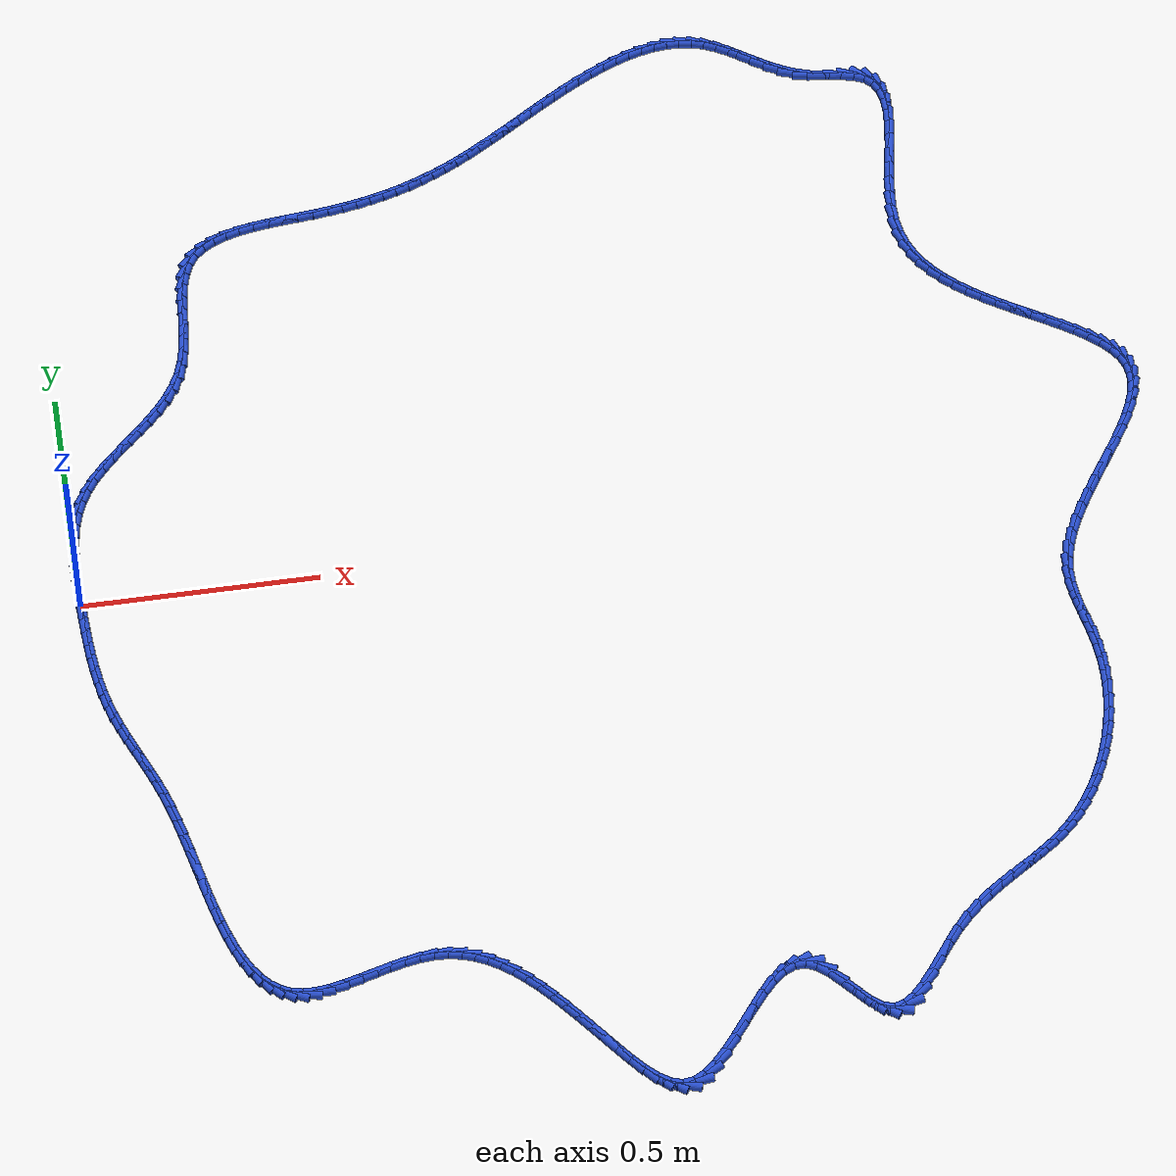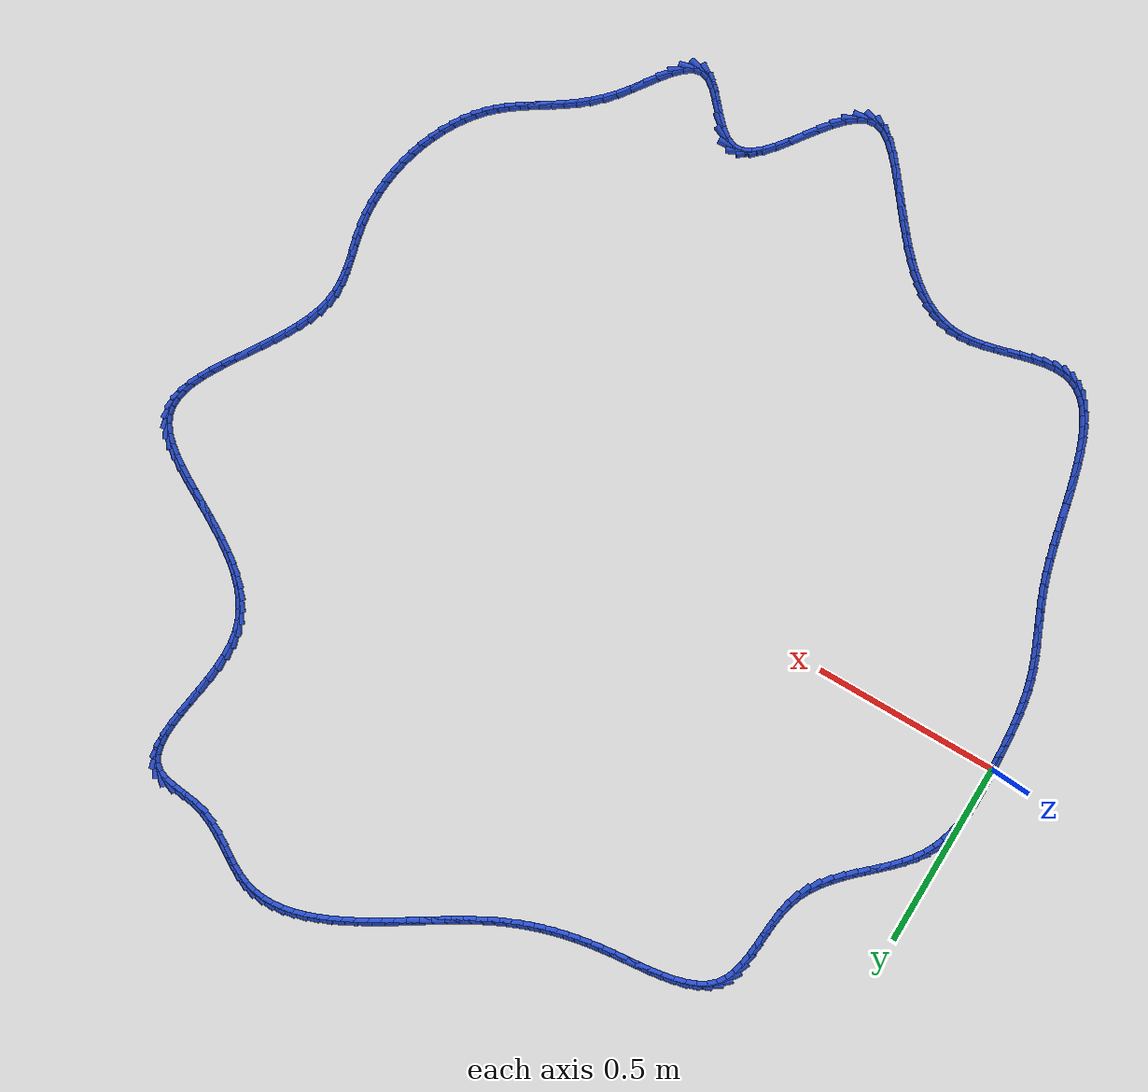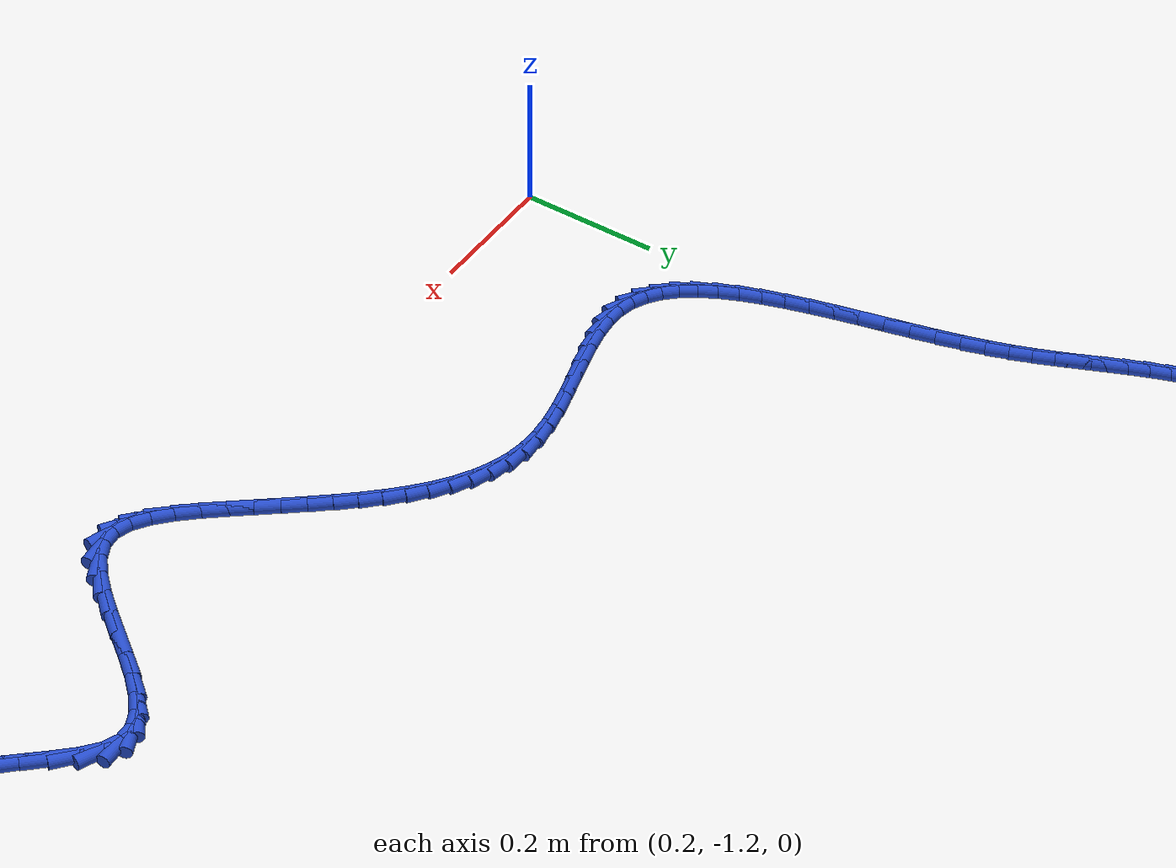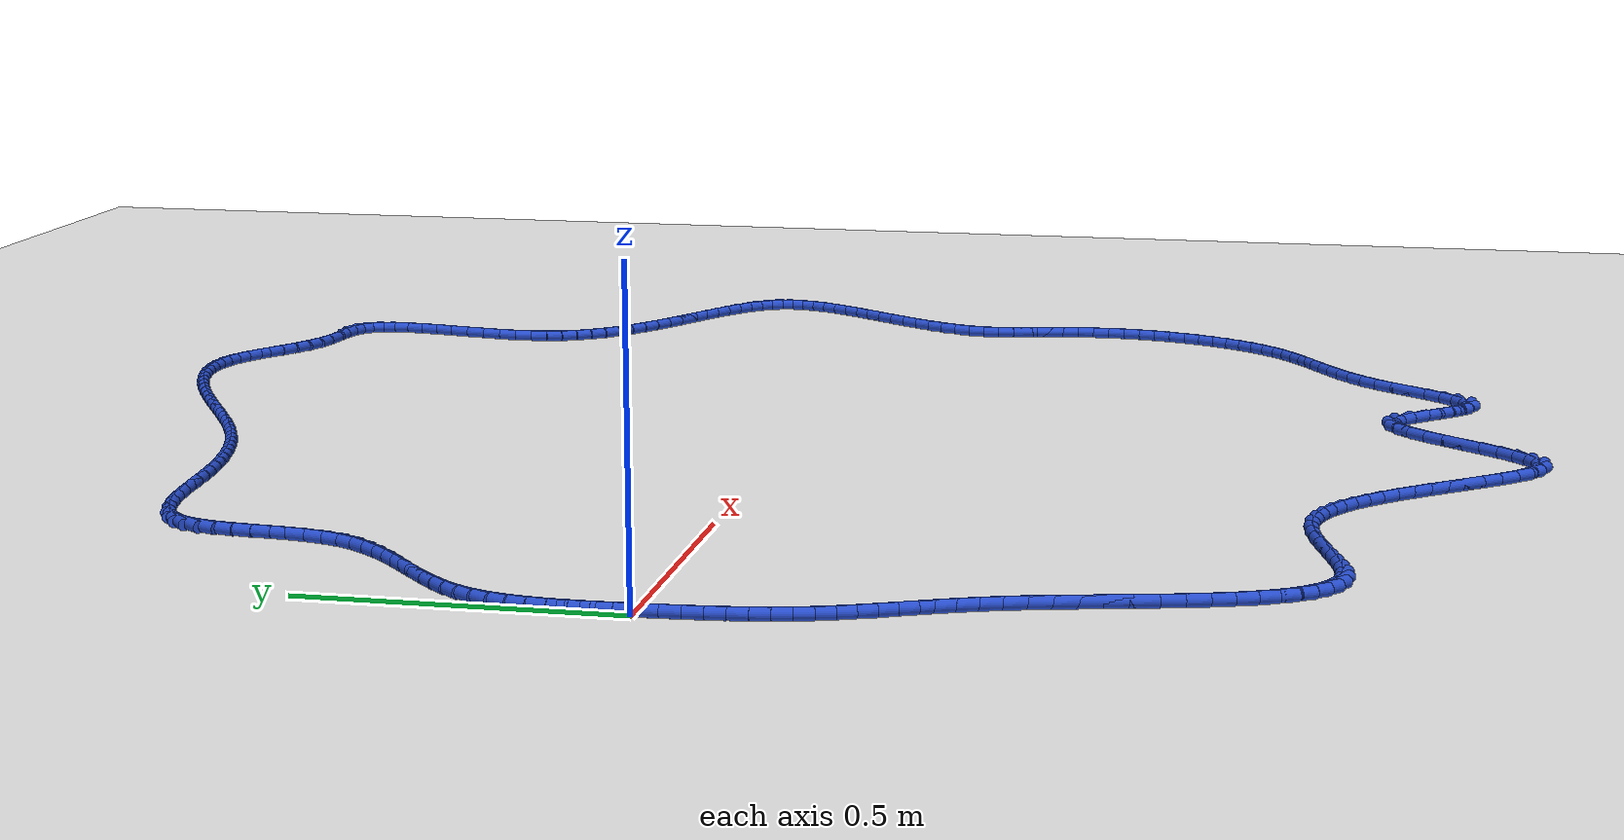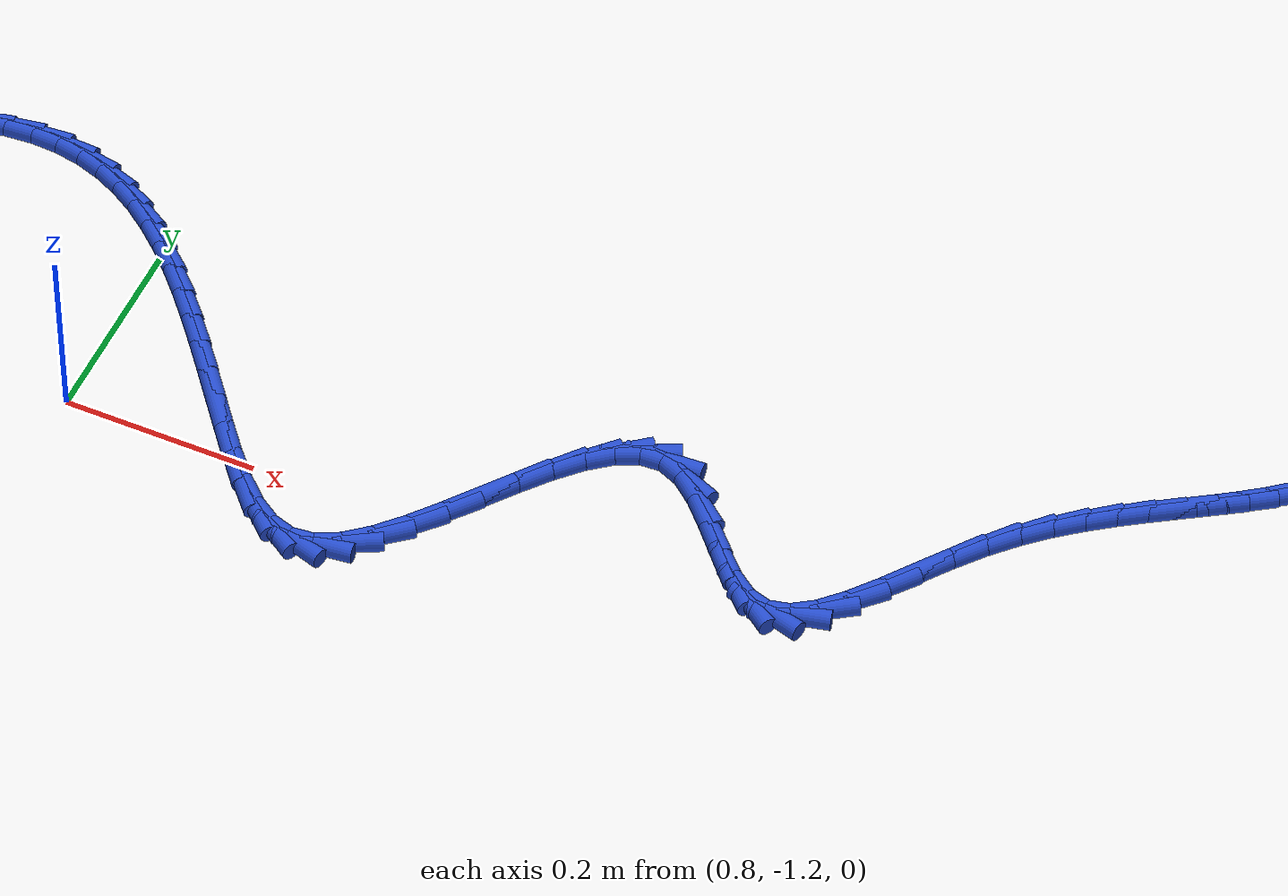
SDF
<sdf version="1.6">
 <world name="default">
  <light name="sun" type="directional">
   <pose>0 0 10 0 -0 0</pose>
   <diffuse>0.8 0.8 0.8 1</diffuse>
   <specular>0.2 0.2 0.2 1</specular>
   <attenuation>
    <range>1000</range>
    <constant>0.9</constant>
    <linear>0.01</linear>
    <quadratic>0.001</quadratic>
   </attenuation>
   <direction>-0.5 0.1 -0.9</direction>
  </light>
  <model name="ground_plane">
   <static>1</static>
   <link name="link">
    <collision name="collision">
     <geometry><plane><normal>0 0 1</normal><size>100 100</size></plane></geometry>
     <surface><friction><ode><mu>100</mu><mu2>50</mu2></ode></friction></surface>
    </collision>
    <visual name="visual">
     <cast_shadows>0</cast_shadows>
     <geometry><plane><normal>0 0 1</normal><size>100 100</size></plane></geometry>
     <material>
      <script><uri>file://media/materials/scripts/gazebo.material</uri><name>Gazebo/WhiteGlow</name></script>
     </material>
    </visual>
   </link>
  </model>
  <gravity>0 0 -9.8</gravity>
  <magnetic_field>6e-06 2.3e-05 -4.2e-05</magnetic_field>
  <atmosphere type="adiabatic"/>
  <physics name="default_physics" default="0" type="ode">
   <max_step_size>0.001</max_step_size>
   <real_time_factor>1</real_time_factor>
   <real_time_update_rate>1000</real_time_update_rate>
  </physics>
  <scene><ambient>0.4 0.4 0.4 1</ambient><background>0.7 0.7 0.7 1</background><shadows>1</shadows></scene>
  <spherical_coordinates>
   <surface_model>EARTH_WGS84</surface_model>
   <latitude_deg>0</latitude_deg>
   <longitude_deg>0</longitude_deg>
   <elevation>0</elevation>
   <heading_deg>0</heading_deg>
  </spherical_coordinates>
  <model name="line">
   <link name="link_0">
    <pose>-1.3877787807814457e-17 -2.0816681711721685e-17 0.01 0 1.57 -1.5352226117898293</pose>
    <collision name="collision">
     <geometry><cylinder><radius>0.01</radius><length>0.08</length></cylinder></geometry>
    </collision>
    <visual name="visual">
     <material>
      <script><name>Gazebo/Blue</name><uri>file://media/materials/scripts/gazebo.material</uri></script>
     </material>
     <geometry><cylinder><radius>0.01</radius><length>0.08</length></cylinder></geometry>
    </visual>
   </link>
   <link name="link_1">
    <pose>-0.001136323410570814 0.0319293060891615 0.01 0 1.57 -1.5522565801094093</pose>
    <collision name="collision">
     <geometry><cylinder><radius>0.01</radius><length>0.08</length></cylinder></geometry>
    </collision>
    <visual name="visual">
     <material>
      <script><name>Gazebo/Blue</name><uri>file://media/materials/scripts/gazebo.material</uri></script>
     </material>
     <geometry><cylinder><radius>0.01</radius><length>0.08</length></cylinder></geometry>
    </visual>
   </link>
   <link name="link_2">
    <pose>-0.001728566261842261 0.06387014131679172 0.01 0 1.57 1.5598440946815808</pose>
    <collision name="collision">
     <geometry><cylinder><radius>0.01</radius><length>0.08</length></cylinder></geometry>
    </collision>
    <visual name="visual">
     <material>
      <script><name>Gazebo/Blue</name><uri>file://media/materials/scripts/gazebo.material</uri></script>
     </material>
     <geometry><cylinder><radius>0.01</radius><length>0.08</length></cylinder></geometry>
    </visual>
   </link>
   <link name="link_3">
    <pose>-0.0013812105346205877 0.09558439234035589 0.01 0 1.57 1.5170083752851309</pose>
    <collision name="collision">
     <geometry><cylinder><radius>0.01</radius><length>0.08</length></cylinder></geometry>
    </collision>
    <visual name="visual">
     <material>
      <script><name>Gazebo/Blue</name><uri>file://media/materials/scripts/gazebo.material</uri></script>
     </material>
     <geometry><cylinder><radius>0.01</radius><length>0.08</length></cylinder></geometry>
    </visual>
   </link>
   <link name="link_4">
    <pose>0.00030126179028797627 0.12683394581731922 0.01 0 1.57 1.459523945433175</pose>
    <collision name="collision">
     <geometry><cylinder><radius>0.01</radius><length>0.08</length></cylinder></geometry>
    </collision>
    <visual name="visual">
     <material>
      <script><name>Gazebo/Blue</name><uri>file://media/materials/scripts/gazebo.material</uri></script>
     </material>
     <geometry><cylinder><radius>0.01</radius><length>0.08</length></cylinder></geometry>
    </visual>
   </link>
   <link name="link_5">
    <pose>0.0037143687320771966 0.15738068840514685 0.01 0 1.57 1.3858344620848655</pose>
    <collision name="collision">
     <geometry><cylinder><radius>0.01</radius><length>0.08</length></cylinder></geometry>
    </collision>
    <visual name="visual">
     <material>
      <script><name>Gazebo/Blue</name><uri>file://media/materials/scripts/gazebo.material</uri></script>
     </material>
     <geometry><cylinder><radius>0.01</radius><length>0.08</length></cylinder></geometry>
    </visual>
   </link>
   <link name="link_6">
    <pose>0.00925362830994085 0.18698650676130396 0.01 0 1.57 1.2944819344400007</pose>
    <collision name="collision">
     <geometry><cylinder><radius>0.01</radius><length>0.08</length></cylinder></geometry>
    </collision>
    <visual name="visual">
     <material>
      <script><name>Gazebo/Blue</name><uri>file://media/materials/scripts/gazebo.material</uri></script>
     </material>
     <geometry><cylinder><radius>0.01</radius><length>0.08</length></cylinder></geometry>
    </visual>
   </link>
   <link name="link_7">
    <pose>0.0173145585430727 0.21541328754325575 0.01 0 1.57 1.1847402585053743</pose>
    <collision name="collision">
     <geometry><cylinder><radius>0.01</radius><length>0.08</length></cylinder></geometry>
    </collision>
    <visual name="visual">
     <material>
      <script><name>Gazebo/Blue</name><uri>file://media/materials/scripts/gazebo.material</uri></script>
     </material>
     <geometry><cylinder><radius>0.01</radius><length>0.08</length></cylinder></geometry>
    </visual>
   </link>
   <link name="link_8">
    <pose>0.02829267745066652 0.24242291740846747 0.01 0 1.57 1.0603880104524492</pose>
    <collision name="collision">
     <geometry><cylinder><radius>0.01</radius><length>0.08</length></cylinder></geometry>
    </collision>
    <visual name="visual">
     <material>
      <script><name>Gazebo/Blue</name><uri>file://media/materials/scripts/gazebo.material</uri></script>
     </material>
     <geometry><cylinder><radius>0.01</radius><length>0.08</length></cylinder></geometry>
    </visual>
   </link>
   <link name="link_9">
    <pose>0.0425114001692829 0.26781825942759047 0.01 0 1.57 0.9483036169660058</pose>
    <collision name="collision">
     <geometry><cylinder><radius>0.01</radius><length>0.08</length></cylinder></geometry>
    </collision>
    <visual name="visual">
     <material>
      <script><name>Gazebo/Blue</name><uri>file://media/materials/scripts/gazebo.material</uri></script>
     </material>
     <geometry><cylinder><radius>0.01</radius><length>0.08</length></cylinder></geometry>
    </visual>
   </link>
   <link name="link_10">
    <pose>0.05968537244002771 0.2917481432314513 0.01 0 1.57 0.8620050192902241</pose>
    <collision name="collision">
     <geometry><cylinder><radius>0.01</radius><length>0.08</length></cylinder></geometry>
    </collision>
    <visual name="visual">
     <material>
      <script><name>Gazebo/Blue</name><uri>file://media/materials/scripts/gazebo.material</uri></script>
     </material>
     <geometry><cylinder><radius>0.01</radius><length>0.08</length></cylinder></geometry>
    </visual>
   </link>
   <link name="link_11">
    <pose>0.07922357982822038 0.3145351065912478 0.01 0 1.57 0.8006190132701884</pose>
    <collision name="collision">
     <geometry><cylinder><radius>0.01</radius><length>0.08</length></cylinder></geometry>
    </collision>
    <visual name="visual">
     <material>
      <script><name>Gazebo/Blue</name><uri>file://media/materials/scripts/gazebo.material</uri></script>
     </material>
     <geometry><cylinder><radius>0.01</radius><length>0.08</length></cylinder></geometry>
    </visual>
   </link>
   <link name="link_12">
    <pose>0.10053270528436065 0.33650299586519655 0.01 0 1.57 0.7623340318087835</pose>
    <collision name="collision">
     <geometry><cylinder><radius>0.01</radius><length>0.08</length></cylinder></geometry>
    </collision>
    <visual name="visual">
     <material>
      <script><name>Gazebo/Blue</name><uri>file://media/materials/scripts/gazebo.material</uri></script>
     </material>
     <geometry><cylinder><radius>0.01</radius><length>0.08</length></cylinder></geometry>
    </visual>
   </link>
   <link name="link_13">
    <pose>0.12301943175894825 0.35797565741151466 0.01 0 1.57 0.7455356103986092</pose>
    <collision name="collision">
     <geometry><cylinder><radius>0.01</radius><length>0.08</length></cylinder></geometry>
    </collision>
    <visual name="visual">
     <material>
      <script><name>Gazebo/Blue</name><uri>file://media/materials/scripts/gazebo.material</uri></script>
     </material>
     <geometry><cylinder><radius>0.01</radius><length>0.08</length></cylinder></geometry>
    </visual>
   </link>
   <link name="link_14">
    <pose>0.14609044220248293 0.37927693758841907 0.01 0 1.57 0.7492865835895974</pose>
    <collision name="collision">
     <geometry><cylinder><radius>0.01</radius><length>0.08</length></cylinder></geometry>
    </collision>
    <visual name="visual">
     <material>
      <script><name>Gazebo/Blue</name><uri>file://media/materials/scripts/gazebo.material</uri></script>
     </material>
     <geometry><cylinder><radius>0.01</radius><length>0.08</length></cylinder></geometry>
    </visual>
   </link>
   <link name="link_15">
    <pose>0.1691524195654644 0.4007306827541263 0.01 0 1.57 0.7734686889386954</pose>
    <collision name="collision">
     <geometry><cylinder><radius>0.01</radius><length>0.08</length></cylinder></geometry>
    </collision>
    <visual name="visual">
     <material>
      <script><name>Gazebo/Blue</name><uri>file://media/materials/scripts/gazebo.material</uri></script>
     </material>
     <geometry><cylinder><radius>0.01</radius><length>0.08</length></cylinder></geometry>
    </visual>
   </link>
   <link name="link_16">
    <pose>0.19161204679839247 0.42266073926685366 0.01 0 1.57 0.818714202508982</pose>
    <collision name="collision">
     <geometry><cylinder><radius>0.01</radius><length>0.08</length></cylinder></geometry>
    </collision>
    <visual name="visual">
     <material>
      <script><name>Gazebo/Blue</name><uri>file://media/materials/scripts/gazebo.material</uri></script>
     </material>
     <geometry><cylinder><radius>0.01</radius><length>0.08</length></cylinder></geometry>
    </visual>
   </link>
   <link name="link_17">
    <pose>0.21287600685176686 0.44539095348481805 0.01 0 1.57 0.8861252138588503</pose>
    <collision name="collision">
     <geometry><cylinder><radius>0.01</radius><length>0.08</length></cylinder></geometry>
    </collision>
    <visual name="visual">
     <material>
      <script><name>Gazebo/Blue</name><uri>file://media/materials/scripts/gazebo.material</uri></script>
     </material>
     <geometry><cylinder><radius>0.01</radius><length>0.08</length></cylinder></geometry>
    </visual>
   </link>
   <link name="link_18">
    <pose>0.23235098267608725 0.4692451717662358 0.01 0 1.57 0.9766726559810752</pose>
    <collision name="collision">
     <geometry><cylinder><radius>0.01</radius><length>0.08</length></cylinder></geometry>
    </collision>
    <visual name="visual">
     <material>
      <script><name>Gazebo/Blue</name><uri>file://media/materials/scripts/gazebo.material</uri></script>
     </material>
     <geometry><cylinder><radius>0.01</radius><length>0.08</length></cylinder></geometry>
    </visual>
   </link>
   <link name="link_19">
    <pose>0.24944365722185338 0.49454724046932447 0.01 0 1.57 1.090152566953872</pose>
    <collision name="collision">
     <geometry><cylinder><radius>0.01</radius><length>0.08</length></cylinder></geometry>
    </collision>
    <visual name="visual">
     <material>
      <script><name>Gazebo/Blue</name><uri>file://media/materials/scripts/gazebo.material</uri></script>
     </material>
     <geometry><cylinder><radius>0.01</radius><length>0.08</length></cylinder></geometry>
    </visual>
   </link>
   <link name="link_20">
    <pose>0.26356071343956516 0.5216210059523008 0.01 0 1.57 1.222939860125851</pose>
    <collision name="collision">
     <geometry><cylinder><radius>0.01</radius><length>0.08</length></cylinder></geometry>
    </collision>
    <visual name="visual">
     <material>
      <script><name>Gazebo/Blue</name><uri>file://media/materials/scripts/gazebo.material</uri></script>
     </material>
     <geometry><cylinder><radius>0.01</radius><length>0.08</length></cylinder></geometry>
    </visual>
   </link>
   <link name="link_21">
    <pose>0.2741319722686062 0.5507749570641272 0.01 0 1.57 1.3444795407717574</pose>
    <collision name="collision">
     <geometry><cylinder><radius>0.01</radius><length>0.08</length></cylinder></geometry>
    </collision>
    <visual name="visual">
     <material>
      <script><name>Gazebo/Blue</name><uri>file://media/materials/scripts/gazebo.material</uri></script>
     </material>
     <geometry><cylinder><radius>0.01</radius><length>0.08</length></cylinder></geometry>
    </visual>
   </link>
   <link name="link_22">
    <pose>0.28128793871310515 0.5818525136254166 0.01 0 1.57 1.4269185933812407</pose>
    <collision name="collision">
     <geometry><cylinder><radius>0.01</radius><length>0.08</length></cylinder></geometry>
    </collision>
    <visual name="visual">
     <material>
      <script><name>Gazebo/Blue</name><uri>file://media/materials/scripts/gazebo.material</uri></script>
     </material>
     <geometry><cylinder><radius>0.01</radius><length>0.08</length></cylinder></geometry>
    </visual>
   </link>
   <link name="link_23">
    <pose>0.28596858367131384 0.6141598240447349 0.01 0 1.57 1.4738742626520873</pose>
    <collision name="collision">
     <geometry><cylinder><radius>0.01</radius><length>0.08</length></cylinder></geometry>
    </collision>
    <visual name="visual">
     <material>
      <script><name>Gazebo/Blue</name><uri>file://media/materials/scripts/gazebo.material</uri></script>
     </material>
     <geometry><cylinder><radius>0.01</radius><length>0.08</length></cylinder></geometry>
    </visual>
   </link>
   <link name="link_24">
    <pose>0.28915891454185294 0.6469731443975407 0.01 0 1.57 1.4886080291845232</pose>
    <collision name="collision">
     <geometry><cylinder><radius>0.01</radius><length>0.08</length></cylinder></geometry>
    </collision>
    <visual name="visual">
     <material>
      <script><name>Gazebo/Blue</name><uri>file://media/materials/scripts/gazebo.material</uri></script>
     </material>
     <geometry><cylinder><radius>0.01</radius><length>0.08</length></cylinder></geometry>
    </visual>
   </link>
   <link name="link_25">
    <pose>0.29184393872334274 0.6795687307592925 0.01 0 1.57 1.4711491300775834</pose>
    <collision name="collision">
     <geometry><cylinder><radius>0.01</radius><length>0.08</length></cylinder></geometry>
    </collision>
    <visual name="visual">
     <material>
      <script><name>Gazebo/Blue</name><uri>file://media/materials/scripts/gazebo.material</uri></script>
     </material>
     <geometry><cylinder><radius>0.01</radius><length>0.08</length></cylinder></geometry>
    </visual>
   </link>
   <link name="link_26">
    <pose>0.2950086636144039 0.7112228392054489 0.01 0 1.57 1.4176337225959348</pose>
    <collision name="collision">
     <geometry><cylinder><radius>0.01</radius><length>0.08</length></cylinder></geometry>
    </collision>
    <visual name="visual">
     <material>
      <script><name>Gazebo/Blue</name><uri>file://media/materials/scripts/gazebo.material</uri></script>
     </material>
     <geometry><cylinder><radius>0.01</radius><length>0.08</length></cylinder></geometry>
    </visual>
   </link>
   <link name="link_27">
    <pose>0.29963809661365665 0.741211725811468 0.01 0 1.57 1.3197172940842834</pose>
    <collision name="collision">
     <geometry><cylinder><radius>0.01</radius><length>0.08</length></cylinder></geometry>
    </collision>
    <visual name="visual">
     <material>
      <script><name>Gazebo/Blue</name><uri>file://media/materials/scripts/gazebo.material</uri></script>
     </material>
     <geometry><cylinder><radius>0.01</radius><length>0.08</length></cylinder></geometry>
    </visual>
   </link>
   <link name="link_28">
    <pose>0.30671724511972154 0.7688116466528091 0.01 0 1.57 1.1652370607983884</pose>
    <collision name="collision">
     <geometry><cylinder><radius>0.01</radius><length>0.08</length></cylinder></geometry>
    </collision>
    <visual name="visual">
     <material>
      <script><name>Gazebo/Blue</name><uri>file://media/materials/scripts/gazebo.material</uri></script>
     </material>
     <geometry><cylinder><radius>0.01</radius><length>0.08</length></cylinder></geometry>
    </visual>
   </link>
   <link name="link_29">
    <pose>0.31723111653121905 0.7932988578049303 0.01 0 1.57 0.9463632395428874</pose>
    <collision name="collision">
     <geometry><cylinder><radius>0.01</radius><length>0.08</length></cylinder></geometry>
    </collision>
    <visual name="visual">
     <material>
      <script><name>Gazebo/Blue</name><uri>file://media/materials/scripts/gazebo.material</uri></script>
     </material>
     <geometry><cylinder><radius>0.01</radius><length>0.08</length></cylinder></geometry>
    </visual>
   </link>
   <link name="link_30">
    <pose>0.33213112186709315 0.8139754250057988 0.01 0 1.57 0.7105518239178906</pose>
    <collision name="collision">
     <geometry><cylinder><radius>0.01</radius><length>0.08</length></cylinder></geometry>
    </collision>
    <visual name="visual">
     <material>
      <script><name>Gazebo/Blue</name><uri>file://media/materials/scripts/gazebo.material</uri></script>
     </material>
     <geometry><cylinder><radius>0.01</radius><length>0.08</length></cylinder></geometry>
    </visual>
   </link>
   <link name="link_31">
    <pose>0.35160353398793087 0.8307312141620331 0.01 0 1.57 0.5158622574108703</pose>
    <collision name="collision">
     <geometry><cylinder><radius>0.01</radius><length>0.08</length></cylinder></geometry>
    </collision>
    <visual name="visual">
     <material>
      <script><name>Gazebo/Blue</name><uri>file://media/materials/scripts/gazebo.material</uri></script>
     </material>
     <geometry><cylinder><radius>0.01</radius><length>0.08</length></cylinder></geometry>
    </visual>
   </link>
   <link name="link_32">
    <pose>0.375073674381191 0.8440406749453857 0.01 0 1.57 0.3682051923920951</pose>
    <collision name="collision">
     <geometry><cylinder><radius>0.01</radius><length>0.08</length></cylinder></geometry>
    </collision>
    <visual name="visual">
     <material>
      <script><name>Gazebo/Blue</name><uri>file://media/materials/scripts/gazebo.material</uri></script>
     </material>
     <geometry><cylinder><radius>0.01</radius><length>0.08</length></cylinder></geometry>
    </visual>
   </link>
   <link name="link_33">
    <pose>0.4019341055196044 0.8544034234033431 0.01 0 1.57 0.2609417602958283</pose>
    <collision name="collision">
     <geometry><cylinder><radius>0.01</radius><length>0.08</length></cylinder></geometry>
    </collision>
    <visual name="visual">
     <material>
      <script><name>Gazebo/Blue</name><uri>file://media/materials/scripts/gazebo.material</uri></script>
     </material>
     <geometry><cylinder><radius>0.01</radius><length>0.08</length></cylinder></geometry>
    </visual>
   </link>
   <link name="link_34">
    <pose>0.431577389875902 0.8623190755833914 0.01 0 1.57 0.1854137010561462</pose>
    <collision name="collision">
     <geometry><cylinder><radius>0.01</radius><length>0.08</length></cylinder></geometry>
    </collision>
    <visual name="visual">
     <material>
      <script><name>Gazebo/Blue</name><uri>file://media/materials/scripts/gazebo.material</uri></script>
     </material>
     <geometry><cylinder><radius>0.01</radius><length>0.08</length></cylinder></geometry>
    </visual>
   </link>
   <link name="link_35">
    <pose>0.46339608992281495 0.8682872475330174 0.01 0 1.57 0.13457423957374307</pose>
    <collision name="collision">
     <geometry><cylinder><radius>0.01</radius><length>0.08</length></cylinder></geometry>
    </collision>
    <visual name="visual">
     <material>
      <script><name>Gazebo/Blue</name><uri>file://media/materials/scripts/gazebo.material</uri></script>
     </material>
     <geometry><cylinder><radius>0.01</radius><length>0.08</length></cylinder></geometry>
    </visual>
   </link>
   <link name="link_36">
    <pose>0.4967827681330741 0.8728075552997079 0.01 0 1.57 0.10362598733923199</pose>
    <collision name="collision">
     <geometry><cylinder><radius>0.01</radius><length>0.08</length></cylinder></geometry>
    </collision>
    <visual name="visual">
     <material>
      <script><name>Gazebo/Blue</name><uri>file://media/materials/scripts/gazebo.material</uri></script>
     </material>
     <geometry><cylinder><radius>0.01</radius><length>0.08</length></cylinder></geometry>
    </visual>
   </link>
   <link name="link_37">
    <pose>0.5311299869794104 0.8763796149309488 0.01 0 1.57 0.08976956787255058</pose>
    <collision name="collision">
     <geometry><cylinder><radius>0.01</radius><length>0.08</length></cylinder></geometry>
    </collision>
    <visual name="visual">
     <material>
      <script><name>Gazebo/Blue</name><uri>file://media/materials/scripts/gazebo.material</uri></script>
     </material>
     <geometry><cylinder><radius>0.01</radius><length>0.08</length></cylinder></geometry>
    </visual>
   </link>
   <link name="link_38">
    <pose>0.5658303089345553 0.8795030424742272 0.01 0 1.57 0.09189663974951695</pose>
    <collision name="collision">
     <geometry><cylinder><radius>0.01</radius><length>0.08</length></cylinder></geometry>
    </collision>
    <visual name="visual">
     <material>
      <script><name>Gazebo/Blue</name><uri>file://media/materials/scripts/gazebo.material</uri></script>
     </material>
     <geometry><cylinder><radius>0.01</radius><length>0.08</length></cylinder></geometry>
    </visual>
   </link>
   <link name="link_39">
    <pose>0.6002762964712394 0.8826774539770287 0.01 0 1.57 0.11027783871115762</pose>
    <collision name="collision">
     <geometry><cylinder><radius>0.01</radius><length>0.08</length></cylinder></geometry>
    </collision>
    <visual name="visual">
     <material>
      <script><name>Gazebo/Blue</name><uri>file://media/materials/scripts/gazebo.material</uri></script>
     </material>
     <geometry><cylinder><radius>0.01</radius><length>0.08</length></cylinder></geometry>
    </visual>
   </link>
   <link name="link_40">
    <pose>0.633868531338546 0.8863970234191604 0.01 0 1.57 0.13957708503540867</pose>
    <collision name="collision">
     <geometry><cylinder><radius>0.01</radius><length>0.08</length></cylinder></geometry>
    </collision>
    <visual name="visual">
     <material>
      <script><name>Gazebo/Blue</name><uri>file://media/materials/scripts/gazebo.material</uri></script>
     </material>
     <geometry><cylinder><radius>0.01</radius><length>0.08</length></cylinder></geometry>
    </visual>
   </link>
   <link name="link_41">
    <pose>0.6663050688834656 0.890954052269517 0.01 0 1.57 0.1714658999337202</pose>
    <collision name="collision">
     <geometry><cylinder><radius>0.01</radius><length>0.08</length></cylinder></geometry>
    </collision>
    <visual name="visual">
     <material>
      <script><name>Gazebo/Blue</name><uri>file://media/materials/scripts/gazebo.material</uri></script>
     </material>
     <geometry><cylinder><radius>0.01</radius><length>0.08</length></cylinder></geometry>
    </visual>
   </link>
   <link name="link_42">
    <pose>0.6976623314728139 0.8963840733261758 0.01 0 1.57 0.20517414120906383</pose>
    <collision name="collision">
     <geometry><cylinder><radius>0.01</radius><length>0.08</length></cylinder></geometry>
    </collision>
    <visual name="visual">
     <material>
      <script><name>Gazebo/Blue</name><uri>file://media/materials/scripts/gazebo.material</uri></script>
     </material>
     <geometry><cylinder><radius>0.01</radius><length>0.08</length></cylinder></geometry>
    </visual>
   </link>
   <link name="link_43">
    <pose>0.7280412334419588 0.9027059985670012 0.01 0 1.57 0.24042346776079332</pose>
    <collision name="collision">
     <geometry><cylinder><radius>0.01</radius><length>0.08</length></cylinder></geometry>
    </collision>
    <visual name="visual">
     <material>
      <script><name>Gazebo/Blue</name><uri>file://media/materials/scripts/gazebo.material</uri></script>
     </material>
     <geometry><cylinder><radius>0.01</radius><length>0.08</length></cylinder></geometry>
    </visual>
   </link>
   <link name="link_44">
    <pose>0.7575426891262688 0.9099387399698581 0.01 0 1.57 0.27686193448728175</pose>
    <collision name="collision">
     <geometry><cylinder><radius>0.01</radius><length>0.08</length></cylinder></geometry>
    </collision>
    <visual name="visual">
     <material>
      <script><name>Gazebo/Blue</name><uri>file://media/materials/scripts/gazebo.material</uri></script>
     </material>
     <geometry><cylinder><radius>0.01</radius><length>0.08</length></cylinder></geometry>
    </visual>
   </link>
   <link name="link_45">
    <pose>0.7862676128611118 0.9181012095126104 0.01 0 1.57 0.31407340947982215</pose>
    <collision name="collision">
     <geometry><cylinder><radius>0.01</radius><length>0.08</length></cylinder></geometry>
    </collision>
    <visual name="visual">
     <material>
      <script><name>Gazebo/Blue</name><uri>file://media/materials/scripts/gazebo.material</uri></script>
     </material>
     <geometry><cylinder><radius>0.01</radius><length>0.08</length></cylinder></geometry>
    </visual>
   </link>
   <link name="link_46">
    <pose>0.8143169189818565 0.9272123191731231 0.01 0 1.57 0.3515936774598753</pose>
    <collision name="collision">
     <geometry><cylinder><radius>0.01</radius><length>0.08</length></cylinder></geometry>
    </collision>
    <visual name="visual">
     <material>
      <script><name>Gazebo/Blue</name><uri>file://media/materials/scripts/gazebo.material</uri></script>
     </material>
     <geometry><cylinder><radius>0.01</radius><length>0.08</length></cylinder></geometry>
    </visual>
   </link>
   <link name="link_47">
    <pose>0.8417915218238708 0.9372909809292606 0.01 0 1.57 0.3889320985553688</pose>
    <collision name="collision">
     <geometry><cylinder><radius>0.01</radius><length>0.08</length></cylinder></geometry>
    </collision>
    <visual name="visual">
     <material>
      <script><name>Gazebo/Blue</name><uri>file://media/materials/scripts/gazebo.material</uri></script>
     </material>
     <geometry><cylinder><radius>0.01</radius><length>0.08</length></cylinder></geometry>
    </visual>
   </link>
   <link name="link_48">
    <pose>0.8687923357225226 0.9483561067588868 0.01 0 1.57 0.4255078160121785</pose>
    <collision name="collision">
     <geometry><cylinder><radius>0.01</radius><length>0.08</length></cylinder></geometry>
    </collision>
    <visual name="visual">
     <material>
      <script><name>Gazebo/Blue</name><uri>file://media/materials/scripts/gazebo.material</uri></script>
     </material>
     <geometry><cylinder><radius>0.01</radius><length>0.08</length></cylinder></geometry>
    </visual>
   </link>
   <link name="link_49">
    <pose>0.8954217869738804 0.9604244442703687 0.01 0 1.57 0.4590977035321406</pose>
    <collision name="collision">
     <geometry><cylinder><radius>0.01</radius><length>0.08</length></cylinder></geometry>
    </collision>
    <visual name="visual">
     <material>
      <script><name>Gazebo/Blue</name><uri>file://media/materials/scripts/gazebo.material</uri></script>
     </material>
     <geometry><cylinder><radius>0.01</radius><length>0.08</length></cylinder></geometry>
    </visual>
   </link>
   <link name="link_50">
    <pose>0.9218122227821428 0.9734699093364947 0.01 0 1.57 0.4877225725304137</pose>
    <collision name="collision">
     <geometry><cylinder><radius>0.01</radius><length>0.08</length></cylinder></geometry>
    </collision>
    <visual name="visual">
     <material>
      <script><name>Gazebo/Blue</name><uri>file://media/materials/scripts/gazebo.material</uri></script>
     </material>
     <geometry><cylinder><radius>0.01</radius><length>0.08</length></cylinder></geometry>
    </visual>
   </link>
   <link name="link_51">
    <pose>0.9481234397770809 0.9874271240180867 0.01 0 1.57 0.5111271799657586</pose>
    <collision name="collision">
     <geometry><cylinder><radius>0.01</radius><length>0.08</length></cylinder></geometry>
    </collision>
    <visual name="visual">
     <material>
      <script><name>Gazebo/Blue</name><uri>file://media/materials/scripts/gazebo.material</uri></script>
     </material>
     <geometry><cylinder><radius>0.01</radius><length>0.08</length></cylinder></geometry>
    </visual>
   </link>
   <link name="link_52">
    <pose>0.9745162511006799 1.002229255240243 0.01 0 1.57 0.5292782355756943</pose>
    <collision name="collision">
     <geometry><cylinder><radius>0.01</radius><length>0.08</length></cylinder></geometry>
    </collision>
    <visual name="visual">
     <material>
      <script><name>Gazebo/Blue</name><uri>file://media/materials/scripts/gazebo.material</uri></script>
     </material>
     <geometry><cylinder><radius>0.01</radius><length>0.08</length></cylinder></geometry>
    </visual>
   </link>
   <link name="link_53">
    <pose>1.0011514698949242 1.01780946992806 0.01 0 1.57 0.5422775603044807</pose>
    <collision name="collision">
     <geometry><cylinder><radius>0.01</radius><length>0.08</length></cylinder></geometry>
    </collision>
    <visual name="visual">
     <material>
      <script><name>Gazebo/Blue</name><uri>file://media/materials/scripts/gazebo.material</uri></script>
     </material>
     <geometry><cylinder><radius>0.01</radius><length>0.08</length></cylinder></geometry>
    </visual>
   </link>
   <link name="link_54">
    <pose>1.028189909301799 1.0341009350066355 0.01 0 1.57 0.5502976972810698</pose>
    <collision name="collision">
     <geometry><cylinder><radius>0.01</radius><length>0.08</length></cylinder></geometry>
    </collision>
    <visual name="visual">
     <material>
      <script><name>Gazebo/Blue</name><uri>file://media/materials/scripts/gazebo.material</uri></script>
     </material>
     <geometry><cylinder><radius>0.01</radius><length>0.08</length></cylinder></geometry>
    </visual>
   </link>
   <link name="link_55">
    <pose>1.0557876978418765 1.0510325891840988 0.01 0 1.57 0.5527604317135062</pose>
    <collision name="collision">
     <geometry><cylinder><radius>0.01</radius><length>0.08</length></cylinder></geometry>
    </collision>
    <visual name="visual">
     <material>
      <script><name>Gazebo/Blue</name><uri>file://media/materials/scripts/gazebo.material</uri></script>
     </material>
     <geometry><cylinder><radius>0.01</radius><length>0.08</length></cylinder></geometry>
    </visual>
   </link>
   <link name="link_56">
    <pose>1.0839817595152514 1.0684257802809096 0.01 0 1.57 0.5491253197104267</pose>
    <collision name="collision">
     <geometry><cylinder><radius>0.01</radius><length>0.08</length></cylinder></geometry>
    </collision>
    <visual name="visual">
     <material>
      <script><name>Gazebo/Blue</name><uri>file://media/materials/scripts/gazebo.material</uri></script>
     </material>
     <geometry><cylinder><radius>0.01</radius><length>0.08</length></cylinder></geometry>
    </visual>
   </link>
   <link name="link_57">
    <pose>1.1126830776734167 1.0859881853764983 0.01 0 1.57 0.5395536736561675</pose>
    <collision name="collision">
     <geometry><cylinder><radius>0.01</radius><length>0.08</length></cylinder></geometry>
    </collision>
    <visual name="visual">
     <material>
      <script><name>Gazebo/Blue</name><uri>file://media/materials/scripts/gazebo.material</uri></script>
     </material>
     <geometry><cylinder><radius>0.01</radius><length>0.08</length></cylinder></geometry>
    </visual>
   </link>
   <link name="link_58">
    <pose>1.1417966025445394 1.1034220362107106 0.01 0 1.57 0.5239991896611901</pose>
    <collision name="collision">
     <geometry><cylinder><radius>0.01</radius><length>0.08</length></cylinder></geometry>
    </collision>
    <visual name="visual">
     <material>
      <script><name>Gazebo/Blue</name><uri>file://media/materials/scripts/gazebo.material</uri></script>
     </material>
     <geometry><cylinder><radius>0.01</radius><length>0.08</length></cylinder></geometry>
    </visual>
   </link>
   <link name="link_59">
    <pose>1.1712272843567877 1.1204295645233924 0.01 0 1.57 0.5021802407007299</pose>
    <collision name="collision">
     <geometry><cylinder><radius>0.01</radius><length>0.08</length></cylinder></geometry>
    </collision>
    <visual name="visual">
     <material>
      <script><name>Gazebo/Blue</name><uri>file://media/materials/scripts/gazebo.material</uri></script>
     </material>
     <geometry><cylinder><radius>0.01</radius><length>0.08</length></cylinder></geometry>
    </visual>
   </link>
   <link name="link_60">
    <pose>1.2008800733383287 1.1367130020543905 0.01 0 1.57 0.4735817645552316</pose>
    <collision name="collision">
     <geometry><cylinder><radius>0.01</radius><length>0.08</length></cylinder></geometry>
    </collision>
    <visual name="visual">
     <material>
      <script><name>Gazebo/Blue</name><uri>file://media/materials/scripts/gazebo.material</uri></script>
     </material>
     <geometry><cylinder><radius>0.01</radius><length>0.08</length></cylinder></geometry>
    </visual>
   </link>
   <link name="link_61">
    <pose>1.230659919717331 1.1519745805435508 0.01 0 1.57 0.43744638347184744</pose>
    <collision name="collision">
     <geometry><cylinder><radius>0.01</radius><length>0.08</length></cylinder></geometry>
    </collision>
    <visual name="visual">
     <material>
      <script><name>Gazebo/Blue</name><uri>file://media/materials/scripts/gazebo.material</uri></script>
     </material>
     <geometry><cylinder><radius>0.01</radius><length>0.08</length></cylinder></geometry>
    </visual>
   </link>
   <link name="link_62">
    <pose>1.2604717737219613 1.1659165317307187 0.01 0 1.57 0.3927620386258764</pose>
    <collision name="collision">
     <geometry><cylinder><radius>0.01</radius><length>0.08</length></cylinder></geometry>
    </collision>
    <visual name="visual">
     <material>
      <script><name>Gazebo/Blue</name><uri>file://media/materials/scripts/gazebo.material</uri></script>
     </material>
     <geometry><cylinder><radius>0.01</radius><length>0.08</length></cylinder></geometry>
    </visual>
   </link>
   <link name="link_63">
    <pose>1.2902205855803879 1.1782410873557414 0.01 0 1.57 0.33825873249876953</pose>
    <collision name="collision">
     <geometry><cylinder><radius>0.01</radius><length>0.08</length></cylinder></geometry>
    </collision>
    <visual name="visual">
     <material>
      <script><name>Gazebo/Blue</name><uri>file://media/materials/scripts/gazebo.material</uri></script>
     </material>
     <geometry><cylinder><radius>0.01</radius><length>0.08</length></cylinder></geometry>
    </visual>
   </link>
   <link name="link_64">
    <pose>1.319811305520779 1.188650479158465 0.01 0 1.57 0.2724377036952016</pose>
    <collision name="collision">
     <geometry><cylinder><radius>0.01</radius><length>0.08</length></cylinder></geometry>
    </collision>
    <visual name="visual">
     <material>
      <script><name>Gazebo/Blue</name><uri>file://media/materials/scripts/gazebo.material</uri></script>
     </material>
     <geometry><cylinder><radius>0.01</radius><length>0.08</length></cylinder></geometry>
    </visual>
   </link>
   <link name="link_65">
    <pose>1.3491488837713017 1.1968469388787353 0.01 0 1.57 0.19367400843832133</pose>
    <collision name="collision">
     <geometry><cylinder><radius>0.01</radius><length>0.08</length></cylinder></geometry>
    </collision>
    <visual name="visual">
     <material>
      <script><name>Gazebo/Blue</name><uri>file://media/materials/scripts/gazebo.material</uri></script>
     </material>
     <geometry><cylinder><radius>0.01</radius><length>0.08</length></cylinder></geometry>
    </visual>
   </link>
   <link name="link_66">
    <pose>1.3781382705601237 1.2025326982563982 0.01 0 1.57 0.10045509604018234</pose>
    <collision name="collision">
     <geometry><cylinder><radius>0.01</radius><length>0.08</length></cylinder></geometry>
    </collision>
    <visual name="visual">
     <material>
      <script><name>Gazebo/Blue</name><uri>file://media/materials/scripts/gazebo.material</uri></script>
     </material>
     <geometry><cylinder><radius>0.01</radius><length>0.08</length></cylinder></geometry>
    </visual>
   </link>
   <link name="link_67">
    <pose>1.406684416115413 1.2054099890313004 0.01 0 1.57 -0.008174170871005193</pose>
    <collision name="collision">
     <geometry><cylinder><radius>0.01</radius><length>0.08</length></cylinder></geometry>
    </collision>
    <visual name="visual">
     <material>
      <script><name>Gazebo/Blue</name><uri>file://media/materials/scripts/gazebo.material</uri></script>
     </material>
     <geometry><cylinder><radius>0.01</radius><length>0.08</length></cylinder></geometry>
    </visual>
   </link>
   <link name="link_68">
    <pose>1.4346922706653369 1.2051810429432874 0.01 0 1.57 -0.13194189041989873</pose>
    <collision name="collision">
     <geometry><cylinder><radius>0.01</radius><length>0.08</length></cylinder></geometry>
    </collision>
    <visual name="visual">
     <material>
      <script><name>Gazebo/Blue</name><uri>file://media/materials/scripts/gazebo.material</uri></script>
     </material>
     <geometry><cylinder><radius>0.01</radius><length>0.08</length></cylinder></geometry>
    </visual>
   </link>
   <link name="link_69">
    <pose>1.4620667844380637 1.2015480917322061 0.01 0 1.57 -0.2686118469271271</pose>
    <collision name="collision">
     <geometry><cylinder><radius>0.01</radius><length>0.08</length></cylinder></geometry>
    </collision>
    <visual name="visual">
     <material>
      <script><name>Gazebo/Blue</name><uri>file://media/materials/scripts/gazebo.material</uri></script>
     </material>
     <geometry><cylinder><radius>0.01</radius><length>0.08</length></cylinder></geometry>
    </visual>
   </link>
   <link name="link_70">
    <pose>1.488712907661761 1.1942133671379025 0.01 0 1.57 -0.40600251985540864</pose>
    <collision name="collision">
     <geometry><cylinder><radius>0.01</radius><length>0.08</length></cylinder></geometry>
    </collision>
    <visual name="visual">
     <material>
      <script><name>Gazebo/Blue</name><uri>file://media/materials/scripts/gazebo.material</uri></script>
     </material>
     <geometry><cylinder><radius>0.01</radius><length>0.08</length></cylinder></geometry>
    </visual>
   </link>
   <link name="link_71">
    <pose>1.5146070075155027 1.1830818353837358 0.01 0 1.57 -0.5061212952391865</pose>
    <collision name="collision">
     <geometry><cylinder><radius>0.01</radius><length>0.08</length></cylinder></geometry>
    </collision>
    <visual name="visual">
     <material>
      <script><name>Gazebo/Blue</name><uri>file://media/materials/scripts/gazebo.material</uri></script>
     </material>
     <geometry><cylinder><radius>0.01</radius><length>0.08</length></cylinder></geometry>
    </visual>
   </link>
   <link name="link_72">
    <pose>1.5400498776716243 1.1689794266478952 0.01 0 1.57 -0.5620100213830332</pose>
    <collision name="collision">
     <geometry><cylinder><radius>0.01</radius><length>0.08</length></cylinder></geometry>
    </collision>
    <visual name="visual">
     <material>
      <script><name>Gazebo/Blue</name><uri>file://media/materials/scripts/gazebo.material</uri></script>
     </material>
     <geometry><cylinder><radius>0.01</radius><length>0.08</length></cylinder></geometry>
    </visual>
   </link>
   <link name="link_73">
    <pose>1.5654343877233308 1.1529934511314472 0.01 0 1.57 -0.5781456885529181</pose>
    <collision name="collision">
     <geometry><cylinder><radius>0.01</radius><length>0.08</length></cylinder></geometry>
    </collision>
    <visual name="visual">
     <material>
      <script><name>Gazebo/Blue</name><uri>file://media/materials/scripts/gazebo.material</uri></script>
     </material>
     <geometry><cylinder><radius>0.01</radius><length>0.08</length></cylinder></geometry>
    </visual>
   </link>
   <link name="link_74">
    <pose>1.5911534134475127 1.136211236589358 0.01 0 1.57 -0.55756852805914</pose>
    <collision name="collision">
     <geometry><cylinder><radius>0.01</radius><length>0.08</length></cylinder></geometry>
    </collision>
    <visual name="visual">
     <material>
      <script><name>Gazebo/Blue</name><uri>file://media/materials/scripts/gazebo.material</uri></script>
     </material>
     <geometry><cylinder><radius>0.01</radius><length>0.08</length></cylinder></geometry>
    </visual>
   </link>
   <link name="link_75">
    <pose>1.6175998306210608 1.1197201107765953 0.01 0 1.57 -0.5014784152194947</pose>
    <collision name="collision">
     <geometry><cylinder><radius>0.01</radius><length>0.08</length></cylinder></geometry>
    </collision>
    <visual name="visual">
     <material>
      <script><name>Gazebo/Blue</name><uri>file://media/materials/scripts/gazebo.material</uri></script>
     </material>
     <geometry><cylinder><radius>0.01</radius><length>0.08</length></cylinder></geometry>
    </visual>
   </link>
   <link name="link_76">
    <pose>1.6451665150208648 1.1046074014481273 0.01 0 1.57 -0.4102303487607</pose>
    <collision name="collision">
     <geometry><cylinder><radius>0.01</radius><length>0.08</length></cylinder></geometry>
    </collision>
    <visual name="visual">
     <material>
      <script><name>Gazebo/Blue</name><uri>file://media/materials/scripts/gazebo.material</uri></script>
     </material>
     <geometry><cylinder><radius>0.01</radius><length>0.08</length></cylinder></geometry>
    </visual>
   </link>
   <link name="link_77">
    <pose>1.6742463424238159 1.091960436358921 0.01 0 1.57 -0.2856489374148688</pose>
    <collision name="collision">
     <geometry><cylinder><radius>0.01</radius><length>0.08</length></cylinder></geometry>
    </collision>
    <visual name="visual">
     <material>
      <script><name>Gazebo/Blue</name><uri>file://media/materials/scripts/gazebo.material</uri></script>
     </material>
     <geometry><cylinder><radius>0.01</radius><length>0.08</length></cylinder></geometry>
    </visual>
   </link>
   <link name="link_78">
    <pose>1.7052284845688546 1.0828615892110727 0.01 0 1.57 -0.16854654002653469</pose>
    <collision name="collision">
     <geometry><cylinder><radius>0.01</radius><length>0.08</length></cylinder></geometry>
    </collision>
    <visual name="visual">
     <material>
      <script><name>Gazebo/Blue</name><uri>file://media/materials/scripts/gazebo.material</uri></script>
     </material>
     <geometry><cylinder><radius>0.01</radius><length>0.08</length></cylinder></geometry>
    </visual>
   </link>
   <link name="link_79">
    <pose>1.7377104655341917 1.0773344258810922 0.01 0 1.57 -0.13431611152897188</pose>
    <collision name="collision">
     <geometry><cylinder><radius>0.01</radius><length>0.08</length></cylinder></geometry>
    </collision>
    <visual name="visual">
     <material>
      <script><name>Gazebo/Blue</name><uri>file://media/materials/scripts/gazebo.material</uri></script>
     </material>
     <geometry><cylinder><radius>0.01</radius><length>0.08</length></cylinder></geometry>
    </visual>
   </link>
   <link name="link_80">
    <pose>1.7695203896848555 1.0730359601390402 0.01 0 1.57 -0.19700739526920596</pose>
    <collision name="collision">
     <geometry><cylinder><radius>0.01</radius><length>0.08</length></cylinder></geometry>
    </collision>
    <visual name="visual">
     <material>
      <script><name>Gazebo/Blue</name><uri>file://media/materials/scripts/gazebo.material</uri></script>
     </material>
     <geometry><cylinder><radius>0.01</radius><length>0.08</length></cylinder></geometry>
    </visual>
   </link>
   <link name="link_81">
    <pose>1.7982464584684994 1.0673023419428382 0.01 0 1.57 -0.399677282429138</pose>
    <collision name="collision">
     <geometry><cylinder><radius>0.01</radius><length>0.08</length></cylinder></geometry>
    </collision>
    <visual name="visual">
     <material>
      <script><name>Gazebo/Blue</name><uri>file://media/materials/scripts/gazebo.material</uri></script>
     </material>
     <geometry><cylinder><radius>0.01</radius><length>0.08</length></cylinder></geometry>
    </visual>
   </link>
   <link name="link_82">
    <pose>1.8214907330309549 1.0574836613077576 0.01 0 1.57 -0.7508494806357472</pose>
    <collision name="collision">
     <geometry><cylinder><radius>0.01</radius><length>0.08</length></cylinder></geometry>
    </collision>
    <visual name="visual">
     <material>
      <script><name>Gazebo/Blue</name><uri>file://media/materials/scripts/gazebo.material</uri></script>
     </material>
     <geometry><cylinder><radius>0.01</radius><length>0.08</length></cylinder></geometry>
    </visual>
   </link>
   <link name="link_83">
    <pose>1.8379979883188915 1.042079347557758 0.01 0 1.57 -1.0977352028854512</pose>
    <collision name="collision">
     <geometry><cylinder><radius>0.01</radius><length>0.08</length></cylinder></geometry>
    </collision>
    <visual name="visual">
     <material>
      <script><name>Gazebo/Blue</name><uri>file://media/materials/scripts/gazebo.material</uri></script>
     </material>
     <geometry><cylinder><radius>0.01</radius><length>0.08</length></cylinder></geometry>
    </visual>
   </link>
   <link name="link_84">
    <pose>1.8484909300922305 1.0215782289650457 0.01 0 1.57 -1.3573986489377012</pose>
    <collision name="collision">
     <geometry><cylinder><radius>0.01</radius><length>0.08</length></cylinder></geometry>
    </collision>
    <visual name="visual">
     <material>
      <script><name>Gazebo/Blue</name><uri>file://media/materials/scripts/gazebo.material</uri></script>
     </material>
     <geometry><cylinder><radius>0.01</radius><length>0.08</length></cylinder></geometry>
    </visual>
   </link>
   <link name="link_85">
    <pose>1.8538890969347097 0.996667107871523 0.01 0 1.57 -1.5281137101164577</pose>
    <collision name="collision">
     <geometry><cylinder><radius>0.01</radius><length>0.08</length></cylinder></geometry>
    </collision>
    <visual name="visual">
     <material>
      <script><name>Gazebo/Blue</name><uri>file://media/materials/scripts/gazebo.material</uri></script>
     </material>
     <geometry><cylinder><radius>0.01</radius><length>0.08</length></cylinder></geometry>
    </visual>
   </link>
   <link name="link_86">
    <pose>1.8551120274300636 0.9680327866190906 0.01 0 1.57 1.5066998116914727</pose>
    <collision name="collision">
     <geometry><cylinder><radius>0.01</radius><length>0.08</length></cylinder></geometry>
    </collision>
    <visual name="visual">
     <material>
      <script><name>Gazebo/Blue</name><uri>file://media/materials/scripts/gazebo.material</uri></script>
     </material>
     <geometry><cylinder><radius>0.01</radius><length>0.08</length></cylinder></geometry>
    </visual>
   </link>
   <link name="link_87">
    <pose>1.8530792601620298 0.936362067549651 0.01 0 1.57 1.4430742883095142</pose>
    <collision name="collision">
     <geometry><cylinder><radius>0.01</radius><length>0.08</length></cylinder></geometry>
    </collision>
    <visual name="visual">
     <material>
      <script><name>Gazebo/Blue</name><uri>file://media/materials/scripts/gazebo.material</uri></script>
     </material>
     <geometry><cylinder><radius>0.01</radius><length>0.08</length></cylinder></geometry>
    </visual>
   </link>
   <link name="link_88">
    <pose>1.8487103337143436 0.902341753005106 0.01 0 1.57 1.4100582398535333</pose>
    <collision name="collision">
     <geometry><cylinder><radius>0.01</radius><length>0.08</length></cylinder></geometry>
    </collision>
    <visual name="visual">
     <material>
      <script><name>Gazebo/Blue</name><uri>file://media/materials/scripts/gazebo.material</uri></script>
     </material>
     <geometry><cylinder><radius>0.01</radius><length>0.08</length></cylinder></geometry>
    </visual>
   </link>
   <link name="link_89">
    <pose>1.8429247866707406 0.8666586453273561 0.01 0 1.57 1.401065429838195</pose>
    <collision name="collision">
     <geometry><cylinder><radius>0.01</radius><length>0.08</length></cylinder></geometry>
    </collision>
    <visual name="visual">
     <material>
      <script><name>Gazebo/Blue</name><uri>file://media/materials/scripts/gazebo.material</uri></script>
     </material>
     <geometry><cylinder><radius>0.01</radius><length>0.08</length></cylinder></geometry>
    </visual>
   </link>
   <link name="link_90">
    <pose>1.8366421576149574 0.829999546858304 0.01 0 1.57 1.4135018181118597</pose>
    <collision name="collision">
     <geometry><cylinder><radius>0.01</radius><length>0.08</length></cylinder></geometry>
    </collision>
    <visual name="visual">
     <material>
      <script><name>Gazebo/Blue</name><uri>file://media/materials/scripts/gazebo.material</uri></script>
     </material>
     <geometry><cylinder><radius>0.01</radius><length>0.08</length></cylinder></geometry>
    </visual>
   </link>
   <link name="link_91">
    <pose>1.8307819851307303 0.7930512599398511 0.01 0 1.57 1.4478061755793217</pose>
    <collision name="collision">
     <geometry><cylinder><radius>0.01</radius><length>0.08</length></cylinder></geometry>
    </collision>
    <visual name="visual">
     <material>
      <script><name>Gazebo/Blue</name><uri>file://media/materials/scripts/gazebo.material</uri></script>
     </material>
     <geometry><cylinder><radius>0.01</radius><length>0.08</length></cylinder></geometry>
    </visual>
   </link>
   <link name="link_92">
    <pose>1.8262638078017952 0.7565005869138993 0.01 0 1.57 1.507254080678876</pose>
    <collision name="collision">
     <geometry><cylinder><radius>0.01</radius><length>0.08</length></cylinder></geometry>
    </collision>
    <visual name="visual">
     <material>
      <script><name>Gazebo/Blue</name><uri>file://media/materials/scripts/gazebo.material</uri></script>
     </material>
     <geometry><cylinder><radius>0.01</radius><length>0.08</length></cylinder></geometry>
    </visual>
   </link>
   <link name="link_93">
    <pose>1.8240071642118887 0.7210343301223502 0.01 0 1.57 -1.543368048002458</pose>
    <collision name="collision">
     <geometry><cylinder><radius>0.01</radius><length>0.08</length></cylinder></geometry>
    </collision>
    <visual name="visual">
     <material>
      <script><name>Gazebo/Blue</name><uri>file://media/materials/scripts/gazebo.material</uri></script>
     </material>
     <geometry><cylinder><radius>0.01</radius><length>0.08</length></cylinder></geometry>
    </visual>
   </link>
   <link name="link_94">
    <pose>1.8249315929447463 0.6873392919071054 0.01 0 1.57 -1.4166838713793697</pose>
    <collision name="collision">
     <geometry><cylinder><radius>0.01</radius><length>0.08</length></cylinder></geometry>
    </collision>
    <visual name="visual">
     <material>
      <script><name>Gazebo/Blue</name><uri>file://media/materials/scripts/gazebo.material</uri></script>
     </material>
     <geometry><cylinder><radius>0.01</radius><length>0.08</length></cylinder></geometry>
    </visual>
   </link>
   <link name="link_95">
    <pose>1.8298015882673588 0.6559895937872796 0.01 0 1.57 -1.2775870808216063</pose>
    <collision name="collision">
     <geometry><cylinder><radius>0.01</radius><length>0.08</length></cylinder></geometry>
    </collision>
    <visual name="visual">
     <material>
      <script><name>Gazebo/Blue</name><uri>file://media/materials/scripts/gazebo.material</uri></script>
     </material>
     <geometry><cylinder><radius>0.01</radius><length>0.08</length></cylinder></geometry>
    </visual>
   </link>
   <link name="link_96">
    <pose>1.8385643287218343 0.6269653606087155 0.01 0 1.57 -1.1410682008197186</pose>
    <collision name="collision">
     <geometry><cylinder><radius>0.01</radius><length>0.08</length></cylinder></geometry>
    </collision>
    <visual name="visual">
     <material>
      <script><name>Gazebo/Blue</name><uri>file://media/materials/scripts/gazebo.material</uri></script>
     </material>
     <geometry><cylinder><radius>0.01</radius><length>0.08</length></cylinder></geometry>
    </visual>
   </link>
   <link name="link_97">
    <pose>1.850898647412959 0.6000516930763957 0.01 0 1.57 -1.0136859014835315</pose>
    <collision name="collision">
     <geometry><cylinder><radius>0.01</radius><length>0.08</length></cylinder></geometry>
    </collision>
    <visual name="visual">
     <material>
      <script><name>Gazebo/Blue</name><uri>file://media/materials/scripts/gazebo.material</uri></script>
     </material>
     <geometry><cylinder><radius>0.01</radius><length>0.08</length></cylinder></geometry>
    </visual>
   </link>
   <link name="link_98">
    <pose>1.8664832186826144 0.5750335765119388 0.01 0 1.57 -0.900159494776728</pose>
    <collision name="collision">
     <geometry><cylinder><radius>0.01</radius><length>0.08</length></cylinder></geometry>
    </collision>
    <visual name="visual">
     <material>
      <script><name>Gazebo/Blue</name><uri>file://media/materials/scripts/gazebo.material</uri></script>
     </material>
     <geometry><cylinder><radius>0.01</radius><length>0.08</length></cylinder></geometry>
    </visual>
   </link>
   <link name="link_99">
    <pose>1.88499671687268 0.5516959962369625 0.01 0 1.57 -0.8028633343058532</pose>
    <collision name="collision">
     <geometry><cylinder><radius>0.01</radius><length>0.08</length></cylinder></geometry>
    </collision>
    <visual name="visual">
     <material>
      <script><name>Gazebo/Blue</name><uri>file://media/materials/scripts/gazebo.material</uri></script>
     </material>
     <geometry><cylinder><radius>0.01</radius><length>0.08</length></cylinder></geometry>
    </visual>
   </link>
   <link name="link_100">
    <pose>1.906117816325034 0.5298239375730848 0.01 0 1.57 -0.7222098272818781</pose>
    <collision name="collision">
     <geometry><cylinder><radius>0.01</radius><length>0.08</length></cylinder></geometry>
    </collision>
    <visual name="visual">
     <material>
      <script><name>Gazebo/Blue</name><uri>file://media/materials/scripts/gazebo.material</uri></script>
     </material>
     <geometry><cylinder><radius>0.01</radius><length>0.08</length></cylinder></geometry>
    </visual>
   </link>
   <link name="link_101">
    <pose>1.9295251913815596 0.5092023858419239 0.01 0 1.57 -0.6573991090458607</pose>
    <collision name="collision">
     <geometry><cylinder><radius>0.01</radius><length>0.08</length></cylinder></geometry>
    </collision>
    <visual name="visual">
     <material>
      <script><name>Gazebo/Blue</name><uri>file://media/materials/scripts/gazebo.material</uri></script>
     </material>
     <geometry><cylinder><radius>0.01</radius><length>0.08</length></cylinder></geometry>
    </visual>
   </link>
   <link name="link_102">
    <pose>1.9548975163841358 0.48961632636509783 0.01 0 1.57 -0.6071001802593188</pose>
    <collision name="collision">
     <geometry><cylinder><radius>0.01</radius><length>0.08</length></cylinder></geometry>
    </collision>
    <visual name="visual">
     <material>
      <script><name>Gazebo/Blue</name><uri>file://media/materials/scripts/gazebo.material</uri></script>
     </material>
     <geometry><cylinder><radius>0.01</radius><length>0.08</length></cylinder></geometry>
    </visual>
   </link>
   <link name="link_103">
    <pose>1.981913465674642 0.47085074446422454 0.01 0 1.57 -0.5699047802693901</pose>
    <collision name="collision">
     <geometry><cylinder><radius>0.01</radius><length>0.08</length></cylinder></geometry>
    </collision>
    <visual name="visual">
     <material>
      <script><name>Gazebo/Blue</name><uri>file://media/materials/scripts/gazebo.material</uri></script>
     </material>
     <geometry><cylinder><radius>0.01</radius><length>0.08</length></cylinder></geometry>
    </visual>
   </link>
   <link name="link_104">
    <pose>2.010251713594959 0.45269062546092215 0.01 0 1.57 -0.5445728263517903</pose>
    <collision name="collision">
     <geometry><cylinder><radius>0.01</radius><length>0.08</length></cylinder></geometry>
    </collision>
    <visual name="visual">
     <material>
      <script><name>Gazebo/Blue</name><uri>file://media/materials/scripts/gazebo.material</uri></script>
     </material>
     <geometry><cylinder><radius>0.01</radius><length>0.08</length></cylinder></geometry>
    </visual>
   </link>
   <link name="link_105">
    <pose>2.039590934486966 0.434920954676809 0.01 0 1.57 -0.5301406396188105</pose>
    <collision name="collision">
     <geometry><cylinder><radius>0.01</radius><length>0.08</length></cylinder></geometry>
    </collision>
    <visual name="visual">
     <material>
      <script><name>Gazebo/Blue</name><uri>file://media/materials/scripts/gazebo.material</uri></script>
     </material>
     <geometry><cylinder><radius>0.01</radius><length>0.08</length></cylinder></geometry>
    </visual>
   </link>
   <link name="link_106">
    <pose>2.0696098026925442 0.41732671743350236 0.01 0 1.57 -0.5267003974403813</pose>
    <collision name="collision">
     <geometry><cylinder><radius>0.01</radius><length>0.08</length></cylinder></geometry>
    </collision>
    <visual name="visual">
     <material>
      <script><name>Gazebo/Blue</name><uri>file://media/materials/scripts/gazebo.material</uri></script>
     </material>
     <geometry><cylinder><radius>0.01</radius><length>0.08</length></cylinder></geometry>
    </visual>
   </link>
   <link name="link_107">
    <pose>2.0999188131341695 0.3997022340509509 0.01 0 1.57 -0.5377876126190331</pose>
    <collision name="collision">
     <geometry><cylinder><radius>0.01</radius><length>0.08</length></cylinder></geometry>
    </collision>
    <visual name="visual">
     <material>
      <script><name>Gazebo/Blue</name><uri>file://media/materials/scripts/gazebo.material</uri></script>
     </material>
     <geometry><cylinder><radius>0.01</radius><length>0.08</length></cylinder></geometry>
    </visual>
   </link>
   <link name="link_108">
    <pose>2.129785881011208 0.3818887302227648 0.01 0 1.57 -0.5656257648243175</pose>
    <collision name="collision">
     <geometry><cylinder><radius>0.01</radius><length>0.08</length></cylinder></geometry>
    </collision>
    <visual name="visual">
     <material>
      <script><name>Gazebo/Blue</name><uri>file://media/materials/scripts/gazebo.material</uri></script>
     </material>
     <geometry><cylinder><radius>0.01</radius><length>0.08</length></cylinder></geometry>
    </visual>
   </link>
   <link name="link_109">
    <pose>2.1583715553144747 0.3637421320226151 0.01 0 1.57 -0.6132171819817294</pose>
    <collision name="collision">
     <geometry><cylinder><radius>0.01</radius><length>0.08</length></cylinder></geometry>
    </collision>
    <visual name="visual">
     <material>
      <script><name>Gazebo/Blue</name><uri>file://media/materials/scripts/gazebo.material</uri></script>
     </material>
     <geometry><cylinder><radius>0.01</radius><length>0.08</length></cylinder></geometry>
    </visual>
   </link>
   <link name="link_110">
    <pose>2.1848363474656693 0.3451183706680651 0.01 0 1.57 -0.6860888209851176</pose>
    <collision name="collision">
     <geometry><cylinder><radius>0.01</radius><length>0.08</length></cylinder></geometry>
    </collision>
    <visual name="visual">
     <material>
      <script><name>Gazebo/Blue</name><uri>file://media/materials/scripts/gazebo.material</uri></script>
     </material>
     <geometry><cylinder><radius>0.01</radius><length>0.08</length></cylinder></geometry>
    </visual>
   </link>
   <link name="link_111">
    <pose>2.2083407688864938 0.32587337737667826 0.01 0 1.57 -0.7930961859801333</pose>
    <collision name="collision">
     <geometry><cylinder><radius>0.01</radius><length>0.08</length></cylinder></geometry>
    </collision>
    <visual name="visual">
     <material>
      <script><name>Gazebo/Blue</name><uri>file://media/materials/scripts/gazebo.material</uri></script>
     </material>
     <geometry><cylinder><radius>0.01</radius><length>0.08</length></cylinder></geometry>
    </visual>
   </link>
   <link name="link_112">
    <pose>2.22804533099865 0.30586308336601814 0.01 0 1.57 -0.9466770565785255</pose>
    <collision name="collision">
     <geometry><cylinder><radius>0.01</radius><length>0.08</length></cylinder></geometry>
    </collision>
    <visual name="visual">
     <material>
      <script><name>Gazebo/Blue</name><uri>file://media/materials/scripts/gazebo.material</uri></script>
     </material>
     <geometry><cylinder><radius>0.01</radius><length>0.08</length></cylinder></geometry>
    </visual>
   </link>
   <link name="link_113">
    <pose>2.2431105452238382 0.284943419853648 0.01 0 1.57 -1.1587241691534014</pose>
    <collision name="collision">
     <geometry><cylinder><radius>0.01</radius><length>0.08</length></cylinder></geometry>
    </collision>
    <visual name="visual">
     <material>
      <script><name>Gazebo/Blue</name><uri>file://media/materials/scripts/gazebo.material</uri></script>
     </material>
     <geometry><cylinder><radius>0.01</radius><length>0.08</length></cylinder></geometry>
    </visual>
   </link>
   <link name="link_114">
    <pose>2.2527137906373436 0.2629729079486041 0.01 0 1.57 -1.4019546736167359</pose>
    <collision name="collision">
     <geometry><cylinder><radius>0.01</radius><length>0.08</length></cylinder></geometry>
    </collision>
    <visual name="visual">
     <material>
      <script><name>Gazebo/Blue</name><uri>file://media/materials/scripts/gazebo.material</uri></script>
     </material>
     <geometry><cylinder><radius>0.01</radius><length>0.08</length></cylinder></geometry>
    </visual>
   </link>
   <link name="link_115">
    <pose>2.2566461709952774 0.23990430120960435 0.01 0 1.57 1.5221272723762889</pose>
    <collision name="collision">
     <geometry><cylinder><radius>0.01</radius><length>0.08</length></cylinder></geometry>
    </collision>
    <visual name="visual">
     <material>
      <script><name>Gazebo/Blue</name><uri>file://media/materials/scripts/gazebo.material</uri></script>
     </material>
     <geometry><cylinder><radius>0.01</radius><length>0.08</length></cylinder></geometry>
    </visual>
   </link>
   <link name="link_116">
    <pose>2.2554725564112865 0.21580915874715484 0.01 0 1.57 1.3483132950115322</pose>
    <collision name="collision">
     <geometry><cylinder><radius>0.01</radius><length>0.08</length></cylinder></geometry>
    </collision>
    <visual name="visual">
     <material>
      <script><name>Gazebo/Blue</name><uri>file://media/materials/scripts/gazebo.material</uri></script>
     </material>
     <geometry><cylinder><radius>0.01</radius><length>0.08</length></cylinder></geometry>
    </visual>
   </link>
   <link name="link_117">
    <pose>2.2498072327305594 0.19076662705675954 0.01 0 1.57 1.2179190292926807</pose>
    <collision name="collision">
     <geometry><cylinder><radius>0.01</radius><length>0.08</length></cylinder></geometry>
    </collision>
    <visual name="visual">
     <material>
      <script><name>Gazebo/Blue</name><uri>file://media/materials/scripts/gazebo.material</uri></script>
     </material>
     <geometry><cylinder><radius>0.01</radius><length>0.08</length></cylinder></geometry>
    </visual>
   </link>
   <link name="link_118">
    <pose>2.2402644857982863 0.16485585263392236 0.01 0 1.57 1.1235824274150594</pose>
    <collision name="collision">
     <geometry><cylinder><radius>0.01</radius><length>0.08</length></cylinder></geometry>
    </collision>
    <visual name="visual">
     <material>
      <script><name>Gazebo/Blue</name><uri>file://media/materials/scripts/gazebo.material</uri></script>
     </material>
     <geometry><cylinder><radius>0.01</radius><length>0.08</length></cylinder></geometry>
    </visual>
   </link>
   <link name="link_119">
    <pose>2.2274586014596567 0.13815598197414725 0.01 0 1.57 1.0573900036119586</pose>
    <collision name="collision">
     <geometry><cylinder><radius>0.01</radius><length>0.08</length></cylinder></geometry>
    </collision>
    <visual name="visual">
     <material>
      <script><name>Gazebo/Blue</name><uri>file://media/materials/scripts/gazebo.material</uri></script>
     </material>
     <geometry><cylinder><radius>0.01</radius><length>0.08</length></cylinder></geometry>
    </visual>
   </link>
   <link name="link_120">
    <pose>2.2120038655598595 0.11074616157293851 0.01 0 1.57 1.0131230269130178</pose>
    <collision name="collision">
     <geometry><cylinder><radius>0.01</radius><length>0.08</length></cylinder></geometry>
    </collision>
    <visual name="visual">
     <material>
      <script><name>Gazebo/Blue</name><uri>file://media/materials/scripts/gazebo.material</uri></script>
     </material>
     <geometry><cylinder><radius>0.01</radius><length>0.08</length></cylinder></geometry>
    </visual>
   </link>
   <link name="link_121">
    <pose>2.194514563944084 0.08270553792579931 0.01 0 1.57 0.9864816601835548</pose>
    <collision name="collision">
     <geometry><cylinder><radius>0.01</radius><length>0.08</length></cylinder></geometry>
    </collision>
    <visual name="visual">
     <material>
      <script><name>Gazebo/Blue</name><uri>file://media/materials/scripts/gazebo.material</uri></script>
     </material>
     <geometry><cylinder><radius>0.01</radius><length>0.08</length></cylinder></geometry>
    </visual>
   </link>
   <link name="link_122">
    <pose>2.175604982457519 0.05411325752823394 0.01 0 1.57 0.9747611929047348</pose>
    <collision name="collision">
     <geometry><cylinder><radius>0.01</radius><length>0.08</length></cylinder></geometry>
    </collision>
    <visual name="visual">
     <material>
      <script><name>Gazebo/Blue</name><uri>file://media/materials/scripts/gazebo.material</uri></script>
     </material>
     <geometry><cylinder><radius>0.01</radius><length>0.08</length></cylinder></geometry>
    </visual>
   </link>
   <link name="link_123">
    <pose>2.1558894069453545 0.02504846687574635 0.01 0 1.57 0.9765097873525114</pose>
    <collision name="collision">
     <geometry><cylinder><radius>0.01</radius><length>0.08</length></cylinder></geometry>
    </collision>
    <visual name="visual">
     <material>
      <script><name>Gazebo/Blue</name><uri>file://media/materials/scripts/gazebo.material</uri></script>
     </material>
     <geometry><cylinder><radius>0.01</radius><length>0.08</length></cylinder></geometry>
    </visual>
   </link>
   <link name="link_124">
    <pose>2.13598212325278 -0.004409687536159515 0.01 0 1.57 0.9912949978484613</pose>
    <collision name="collision">
     <geometry><cylinder><radius>0.01</radius><length>0.08</length></cylinder></geometry>
    </collision>
    <visual name="visual">
     <material>
      <script><name>Gazebo/Blue</name><uri>file://media/materials/scripts/gazebo.material</uri></script>
     </material>
     <geometry><cylinder><radius>0.01</radius><length>0.08</length></cylinder></geometry>
    </visual>
   </link>
   <link name="link_125">
    <pose>2.1164974172249846 -0.03418205921197976 0.01 0 1.57 1.0195832186732838</pose>
    <collision name="collision">
     <geometry><cylinder><radius>0.01</radius><length>0.08</length></cylinder></geometry>
    </collision>
    <visual name="visual">
     <material>
      <script><name>Gazebo/Blue</name><uri>file://media/materials/scripts/gazebo.material</uri></script>
     </material>
     <geometry><cylinder><radius>0.01</radius><length>0.08</length></cylinder></geometry>
    </visual>
   </link>
   <link name="link_126">
    <pose>2.098049574707156 -0.06418950165621043 0.01 0 1.57 1.0627035868776613</pose>
    <collision name="collision">
     <geometry><cylinder><radius>0.01</radius><length>0.08</length></cylinder></geometry>
    </collision>
    <visual name="visual">
     <material>
      <script><name>Gazebo/Blue</name><uri>file://media/materials/scripts/gazebo.material</uri></script>
     </material>
     <geometry><cylinder><radius>0.01</radius><length>0.08</length></cylinder></geometry>
    </visual>
   </link>
   <link name="link_127">
    <pose>2.0812528815444877 -0.09435286837334765 0.01 0 1.57 1.1228467254052958</pose>
    <collision name="collision">
     <geometry><cylinder><radius>0.01</radius><length>0.08</length></cylinder></geometry>
    </collision>
    <visual name="visual">
     <material>
      <script><name>Gazebo/Blue</name><uri>file://media/materials/scripts/gazebo.material</uri></script>
     </material>
     <geometry><cylinder><radius>0.01</radius><length>0.08</length></cylinder></geometry>
    </visual>
   </link>
   <link name="link_128">
    <pose>2.0667216235821644 -0.1245930128678874 0.01 0 1.57 1.2029996907922589</pose>
    <collision name="collision">
     <geometry><cylinder><radius>0.01</radius><length>0.08</length></cylinder></geometry>
    </collision>
    <visual name="visual">
     <material>
      <script><name>Gazebo/Blue</name><uri>file://media/materials/scripts/gazebo.material</uri></script>
     </material>
     <geometry><cylinder><radius>0.01</radius><length>0.08</length></cylinder></geometry>
    </visual>
   </link>
   <link name="link_129">
    <pose>2.0550700866653777 -0.1548307886443258 0.01 0 1.57 1.3066104427403022</pose>
    <collision name="collision">
     <geometry><cylinder><radius>0.01</radius><length>0.08</length></cylinder></geometry>
    </collision>
    <visual name="visual">
     <material>
      <script><name>Gazebo/Blue</name><uri>file://media/materials/scripts/gazebo.material</uri></script>
     </material>
     <geometry><cylinder><radius>0.01</radius><length>0.08</length></cylinder></geometry>
    </visual>
   </link>
   <link name="link_130">
    <pose>2.0469125566393163 -0.184987049207159 0.01 0 1.57 1.4364834005660203</pose>
    <collision name="collision">
     <geometry><cylinder><radius>0.01</radius><length>0.08</length></cylinder></geometry>
    </collision>
    <visual name="visual">
     <material>
      <script><name>Gazebo/Blue</name><uri>file://media/materials/scripts/gazebo.material</uri></script>
     </material>
     <geometry><cylinder><radius>0.01</radius><length>0.08</length></cylinder></geometry>
    </visual>
   </link>
   <link name="link_131">
    <pose>2.0428592908488787 -0.21498314081734582 0.01 0 1.57 -1.5662880877214558</pose>
    <collision name="collision">
     <geometry><cylinder><radius>0.01</radius><length>0.08</length></cylinder></geometry>
    </collision>
    <visual name="visual">
     <material>
      <script><name>Gazebo/Blue</name><uri>file://media/materials/scripts/gazebo.material</uri></script>
     </material>
     <geometry><cylinder><radius>0.01</radius><length>0.08</length></cylinder></geometry>
    </visual>
   </link>
   <link name="link_132">
    <pose>2.042993735145489 -0.2448048480502026 0.01 0 1.57 -1.458353848641291</pose>
    <collision name="collision">
     <geometry><cylinder><radius>0.01</radius><length>0.08</length></cylinder></geometry>
    </collision>
    <visual name="visual">
     <material>
      <script><name>Gazebo/Blue</name><uri>file://media/materials/scripts/gazebo.material</uri></script>
     </material>
     <geometry><cylinder><radius>0.01</radius><length>0.08</length></cylinder></geometry>
    </visual>
   </link>
   <link name="link_133">
    <pose>2.0463543030880196 -0.27456578131669085 0.01 0 1.57 -1.3883965175967687</pose>
    <collision name="collision">
     <geometry><cylinder><radius>0.01</radius><length>0.08</length></cylinder></geometry>
    </collision>
    <visual name="visual">
     <material>
      <script><name>Gazebo/Blue</name><uri>file://media/materials/scripts/gazebo.material</uri></script>
     </material>
     <geometry><cylinder><radius>0.01</radius><length>0.08</length></cylinder></geometry>
    </visual>
   </link>
   <link name="link_134">
    <pose>2.0518562287656588 -0.30439461804413015 0.01 0 1.57 -1.3557419510926974</pose>
    <collision name="collision">
     <geometry><cylinder><radius>0.01</radius><length>0.08</length></cylinder></geometry>
    </collision>
    <visual name="visual">
     <material>
      <script><name>Gazebo/Blue</name><uri>file://media/materials/scripts/gazebo.material</uri></script>
     </material>
     <geometry><cylinder><radius>0.01</radius><length>0.08</length></cylinder></geometry>
    </visual>
   </link>
   <link name="link_135">
    <pose>2.058414746267597 -0.33442003565984 0.01 0 1.57 -1.358864344481079</pose>
    <collision name="collision">
     <geometry><cylinder><radius>0.01</radius><length>0.08</length></cylinder></geometry>
    </collision>
    <visual name="visual">
     <material>
      <script><name>Gazebo/Blue</name><uri>file://media/materials/scripts/gazebo.material</uri></script>
     </material>
     <geometry><cylinder><radius>0.01</radius><length>0.08</length></cylinder></geometry>
    </visual>
   </link>
   <link name="link_136">
    <pose>2.0649450896830235 -0.3647707115911403 0.01 0 1.57 -1.3967130495350932</pose>
    <collision name="collision">
     <geometry><cylinder><radius>0.01</radius><length>0.08</length></cylinder></geometry>
    </collision>
    <visual name="visual">
     <material>
      <script><name>Gazebo/Blue</name><uri>file://media/materials/scripts/gazebo.material</uri></script>
     </material>
     <geometry><cylinder><radius>0.01</radius><length>0.08</length></cylinder></geometry>
    </visual>
   </link>
   <link name="link_137">
    <pose>2.0703624931011264 -0.39557532326535033 0.01 0 1.57 -1.464203298205763</pose>
    <collision name="collision">
     <geometry><cylinder><radius>0.01</radius><length>0.08</length></cylinder></geometry>
    </collision>
    <visual name="visual">
     <material>
      <script><name>Gazebo/Blue</name><uri>file://media/materials/scripts/gazebo.material</uri></script>
     </material>
     <geometry><cylinder><radius>0.01</radius><length>0.08</length></cylinder></geometry>
    </visual>
   </link>
   <link name="link_138">
    <pose>2.073716851828532 -0.42692488693848996 0.01 0 1.57 -1.5361477664304273</pose>
    <collision name="collision">
     <geometry><cylinder><radius>0.01</radius><length>0.08</length></cylinder></geometry>
    </collision>
    <visual name="visual">
     <material>
      <script><name>Gazebo/Blue</name><uri>file://media/materials/scripts/gazebo.material</uri></script>
     </material>
     <geometry><cylinder><radius>0.01</radius><length>0.08</length></cylinder></geometry>
    </visual>
   </link>
   <link name="link_139">
    <pose>2.0748181794589025 -0.4586978339400402 0.01 0 1.57 1.5372078605252866</pose>
    <collision name="collision">
     <geometry><cylinder><radius>0.01</radius><length>0.08</length></cylinder></geometry>
    </collision>
    <visual name="visual">
     <material>
      <script><name>Gazebo/Blue</name><uri>file://media/materials/scripts/gazebo.material</uri></script>
     </material>
     <geometry><cylinder><radius>0.01</radius><length>0.08</length></cylinder></geometry>
    </visual>
   </link>
   <link name="link_140">
    <pose>2.0737429359653636 -0.4906980776133069 0.01 0 1.57 1.4719953753841675</pose>
    <collision name="collision">
     <geometry><cylinder><radius>0.01</radius><length>0.08</length></cylinder></geometry>
    </collision>
    <visual name="visual">
     <material>
      <script><name>Gazebo/Blue</name><uri>file://media/materials/scripts/gazebo.material</uri></script>
     </material>
     <geometry><cylinder><radius>0.01</radius><length>0.08</length></cylinder></geometry>
    </visual>
   </link>
   <link name="link_141">
    <pose>2.07056786777336 -0.522729451188479 0.01 0 1.57 1.4090970814213535</pose>
    <collision name="collision">
     <geometry><cylinder><radius>0.01</radius><length>0.08</length></cylinder></geometry>
    </collision>
    <visual name="visual">
     <material>
      <script><name>Gazebo/Blue</name><uri>file://media/materials/scripts/gazebo.material</uri></script>
     </material>
     <geometry><cylinder><radius>0.01</radius><length>0.08</length></cylinder></geometry>
    </visual>
   </link>
   <link name="link_142">
    <pose>2.0653697213083357 -0.5545957878957462 0.01 0 1.57 1.347796023159601</pose>
    <collision name="collision">
     <geometry><cylinder><radius>0.01</radius><length>0.08</length></cylinder></geometry>
    </collision>
    <visual name="visual">
     <material>
      <script><name>Gazebo/Blue</name><uri>file://media/materials/scripts/gazebo.material</uri></script>
     </material>
     <geometry><cylinder><radius>0.01</radius><length>0.08</length></cylinder></geometry>
    </visual>
   </link>
   <link name="link_143">
    <pose>2.058225242995735 -0.5861009209652974 0.01 0 1.57 1.287370537895317</pose>
    <collision name="collision">
     <geometry><cylinder><radius>0.01</radius><length>0.08</length></cylinder></geometry>
    </collision>
    <visual name="visual">
     <material>
      <script><name>Gazebo/Blue</name><uri>file://media/materials/scripts/gazebo.material</uri></script>
     </material>
     <geometry><cylinder><radius>0.01</radius><length>0.08</length></cylinder></geometry>
    </visual>
   </link>
   <link name="link_144">
    <pose>2.049211179261001 -0.6170486836273221 0.01 0 1.57 1.2270896212775317</pose>
    <collision name="collision">
     <geometry><cylinder><radius>0.01</radius><length>0.08</length></cylinder></geometry>
    </collision>
    <visual name="visual">
     <material>
      <script><name>Gazebo/Blue</name><uri>file://media/materials/scripts/gazebo.material</uri></script>
     </material>
     <geometry><cylinder><radius>0.01</radius><length>0.08</length></cylinder></geometry>
    </visual>
   </link>
   <link name="link_145">
    <pose>2.0384042765295796 -0.6472429091120088 0.01 0 1.57 1.1662041826635414</pose>
    <collision name="collision">
     <geometry><cylinder><radius>0.01</radius><length>0.08</length></cylinder></geometry>
    </collision>
    <visual name="visual">
     <material>
      <script><name>Gazebo/Blue</name><uri>file://media/materials/scripts/gazebo.material</uri></script>
     </material>
     <geometry><cylinder><radius>0.01</radius><length>0.08</length></cylinder></geometry>
    </visual>
   </link>
   <link name="link_146">
    <pose>2.025881281226913 -0.6764874306495481 0.01 0 1.57 1.103936204357991</pose>
    <collision name="collision">
     <geometry><cylinder><radius>0.01</radius><length>0.08</length></cylinder></geometry>
    </collision>
    <visual name="visual">
     <material>
      <script><name>Gazebo/Blue</name><uri>file://media/materials/scripts/gazebo.material</uri></script>
     </material>
     <geometry><cylinder><radius>0.01</radius><length>0.08</length></cylinder></geometry>
    </visual>
   </link>
   <link name="link_147">
    <pose>2.011718939778446 -0.7045860814701285 0.01 0 1.57 1.0394678301496818</pose>
    <collision name="collision">
     <geometry><cylinder><radius>0.01</radius><length>0.08</length></cylinder></geometry>
    </collision>
    <visual name="visual">
     <material>
      <script><name>Gazebo/Blue</name><uri>file://media/materials/scripts/gazebo.material</uri></script>
     </material>
     <geometry><cylinder><radius>0.01</radius><length>0.08</length></cylinder></geometry>
    </visual>
   </link>
   <link name="link_148">
    <pose>1.9959939986096227 -0.7313426948039395 0.01 0 1.57 0.9719329601004071</pose>
    <collision name="collision">
     <geometry><cylinder><radius>0.01</radius><length>0.08</length></cylinder></geometry>
    </collision>
    <visual name="visual">
     <material>
      <script><name>Gazebo/Blue</name><uri>file://media/materials/scripts/gazebo.material</uri></script>
     </material>
     <geometry><cylinder><radius>0.01</radius><length>0.08</length></cylinder></geometry>
    </visual>
   </link>
   <link name="link_149">
    <pose>1.978783204145888 -0.7565611038811703 0.01 0 1.57 0.9004151611614566</pose>
    <collision name="collision">
     <geometry><cylinder><radius>0.01</radius><length>0.08</length></cylinder></geometry>
    </collision>
    <visual name="visual">
     <material>
      <script><name>Gazebo/Blue</name><uri>file://media/materials/scripts/gazebo.material</uri></script>
     </material>
     <geometry><cylinder><radius>0.01</radius><length>0.08</length></cylinder></geometry>
    </visual>
   </link>
   <link name="link_150">
    <pose>1.9601633028126848 -0.78004514193201 0.01 0 1.57 0.8239577446351507</pose>
    <collision name="collision">
     <geometry><cylinder><radius>0.01</radius><length>0.08</length></cylinder></geometry>
    </collision>
    <visual name="visual">
     <material>
      <script><name>Gazebo/Blue</name><uri>file://media/materials/scripts/gazebo.material</uri></script>
     </material>
     <geometry><cylinder><radius>0.01</radius><length>0.08</length></cylinder></geometry>
    </visual>
   </link>
   <link name="link_151">
    <pose>1.9402110410354578 -0.8015986421866479 0.01 0 1.57 0.7435692318102812</pose>
    <collision name="collision">
     <geometry><cylinder><radius>0.01</radius><length>0.08</length></cylinder></geometry>
    </collision>
    <visual name="visual">
     <material>
      <script><name>Gazebo/Blue</name><uri>file://media/materials/scripts/gazebo.material</uri></script>
     </material>
     <geometry><cylinder><radius>0.01</radius><length>0.08</length></cylinder></geometry>
    </visual>
   </link>
   <link name="link_152">
    <pose>1.919012973534502 -0.8210935716804751 0.01 0 1.57 0.6727545629571594</pose>
    <collision name="collision">
     <geometry><cylinder><radius>0.01</radius><length>0.08</length></cylinder></geometry>
    </collision>
    <visual name="visual">
     <material>
      <script><name>Gazebo/Blue</name><uri>file://media/materials/scripts/gazebo.material</uri></script>
     </material>
     <geometry><cylinder><radius>0.01</radius><length>0.08</length></cylinder></geometry>
    </visual>
   </link>
   <link name="link_153">
    <pose>1.8967208484368476 -0.8388547666725568 0.01 0 1.57 0.6191066758013075</pose>
    <collision name="collision">
     <geometry><cylinder><radius>0.01</radius><length>0.08</length></cylinder></geometry>
    </collision>
    <visual name="visual">
     <material>
      <script><name>Gazebo/Blue</name><uri>file://media/materials/scripts/gazebo.material</uri></script>
     </material>
     <geometry><cylinder><radius>0.01</radius><length>0.08</length></cylinder></geometry>
    </visual>
   </link>
   <link name="link_154">
    <pose>1.8735130045367376 -0.8553917768066603 0.01 0 1.57 0.5839291045436615</pose>
    <collision name="collision">
     <geometry><cylinder><radius>0.01</radius><length>0.08</length></cylinder></geometry>
    </collision>
    <visual name="visual">
     <material>
      <script><name>Gazebo/Blue</name><uri>file://media/materials/scripts/gazebo.material</uri></script>
     </material>
     <geometry><cylinder><radius>0.01</radius><length>0.08</length></cylinder></geometry>
    </visual>
   </link>
   <link name="link_155">
    <pose>1.849567858994504 -0.8712146961004607 0.01 0 1.57 0.5674680776832267</pose>
    <collision name="collision">
     <geometry><cylinder><radius>0.01</radius><length>0.08</length></cylinder></geometry>
    </collision>
    <visual name="visual">
     <material>
      <script><name>Gazebo/Blue</name><uri>file://media/materials/scripts/gazebo.material</uri></script>
     </material>
     <geometry><cylinder><radius>0.01</radius><length>0.08</length></cylinder></geometry>
    </visual>
   </link>
   <link name="link_156">
    <pose>1.8250638289704784 -0.8868336185716327 0.01 0 1.57 0.5692830103644677</pose>
    <collision name="collision">
     <geometry><cylinder><radius>0.01</radius><length>0.08</length></cylinder></geometry>
    </collision>
    <visual name="visual">
     <material>
      <script><name>Gazebo/Blue</name><uri>file://media/materials/scripts/gazebo.material</uri></script>
     </material>
     <geometry><cylinder><radius>0.01</radius><length>0.08</length></cylinder></geometry>
    </visual>
   </link>
   <link name="link_157">
    <pose>1.8001793316249926 -0.9027586382378504 0.01 0 1.57 0.588467351207862</pose>
    <collision name="collision">
     <geometry><cylinder><radius>0.01</radius><length>0.08</length></cylinder></geometry>
    </collision>
    <visual name="visual">
     <material>
      <script><name>Gazebo/Blue</name><uri>file://media/materials/scripts/gazebo.material</uri></script>
     </material>
     <geometry><cylinder><radius>0.01</radius><length>0.08</length></cylinder></geometry>
    </visual>
   </link>
   <link name="link_158">
    <pose>1.7750927841183777 -0.9194998491167894 0.01 0 1.57 0.6237126060964328</pose>
    <collision name="collision">
     <geometry><cylinder><radius>0.01</radius><length>0.08</length></cylinder></geometry>
    </collision>
    <visual name="visual">
     <material>
      <script><name>Gazebo/Blue</name><uri>file://media/materials/scripts/gazebo.material</uri></script>
     </material>
     <geometry><cylinder><radius>0.01</radius><length>0.08</length></cylinder></geometry>
    </visual>
   </link>
   <link name="link_159">
    <pose>1.7499826036109671 -0.9375673452261242 0.01 0 1.57 0.6732623732489694</pose>
    <collision name="collision">
     <geometry><cylinder><radius>0.01</radius><length>0.08</length></cylinder></geometry>
    </collision>
    <visual name="visual">
     <material>
      <script><name>Gazebo/Blue</name><uri>file://media/materials/scripts/gazebo.material</uri></script>
     </material>
     <geometry><cylinder><radius>0.01</radius><length>0.08</length></cylinder></geometry>
    </visual>
   </link>
   <link name="link_160">
    <pose>1.725027207263091 -0.9574712205835295 0.01 0 1.57 0.7348392455062569</pose>
    <collision name="collision">
     <geometry><cylinder><radius>0.01</radius><length>0.08</length></cylinder></geometry>
    </collision>
    <visual name="visual">
     <material>
      <script><name>Gazebo/Blue</name><uri>file://media/materials/scripts/gazebo.material</uri></script>
     </material>
     <geometry><cylinder><radius>0.01</radius><length>0.08</length></cylinder></geometry>
    </visual>
   </link>
   <link name="link_161">
    <pose>1.7004050122350813 -0.97972156920668 0.01 0 1.57 0.8056390013888878</pose>
    <collision name="collision">
     <geometry><cylinder><radius>0.01</radius><length>0.08</length></cylinder></geometry>
    </collision>
    <visual name="visual">
     <material>
      <script><name>Gazebo/Blue</name><uri>file://media/materials/scripts/gazebo.material</uri></script>
     </material>
     <geometry><cylinder><radius>0.01</radius><length>0.08</length></cylinder></geometry>
    </visual>
   </link>
   <link name="link_162">
    <pose>1.6762944356872709 -1.0048284851132505 0.01 0 1.57 0.8785941583229232</pose>
    <collision name="collision">
     <geometry><cylinder><radius>0.01</radius><length>0.08</length></cylinder></geometry>
    </collision>
    <visual name="visual">
     <material>
      <script><name>Gazebo/Blue</name><uri>file://media/materials/scripts/gazebo.material</uri></script>
     </material>
     <geometry><cylinder><radius>0.01</radius><length>0.08</length></cylinder></geometry>
    </visual>
   </link>
   <link name="link_163">
    <pose>1.6528502306774138 -1.033107049449036 0.01 0 1.57 0.9214966611045057</pose>
    <collision name="collision">
     <geometry><cylinder><radius>0.01</radius><length>0.08</length></cylinder></geometry>
    </collision>
    <visual name="visual">
     <material>
      <script><name>Gazebo/Blue</name><uri>file://media/materials/scripts/gazebo.material</uri></script>
     </material>
     <geometry><cylinder><radius>0.01</radius><length>0.08</length></cylinder></geometry>
    </visual>
   </link>
   <link name="link_164">
    <pose>1.6300217996091817 -1.0631800746306195 0.01 0 1.57 0.923999771573648</pose>
    <collision name="collision">
     <geometry><cylinder><radius>0.01</radius><length>0.08</length></cylinder></geometry>
    </collision>
    <visual name="visual">
     <material>
      <script><name>Gazebo/Blue</name><uri>file://media/materials/scripts/gazebo.material</uri></script>
     </material>
     <geometry><cylinder><radius>0.01</radius><length>0.08</length></cylinder></geometry>
    </visual>
   </link>
   <link name="link_165">
    <pose>1.6076530711334909 -1.0928011772381439 0.01 0 1.57 0.8840874055825223</pose>
    <collision name="collision">
     <geometry><cylinder><radius>0.01</radius><length>0.08</length></cylinder></geometry>
    </collision>
    <visual name="visual">
     <material>
      <script><name>Gazebo/Blue</name><uri>file://media/materials/scripts/gazebo.material</uri></script>
     </material>
     <geometry><cylinder><radius>0.01</radius><length>0.08</length></cylinder></geometry>
    </visual>
   </link>
   <link name="link_166">
    <pose>1.5855871099462924 -1.1197168541083133 0.01 0 1.57 0.7862327432631846</pose>
    <collision name="collision">
     <geometry><cylinder><radius>0.01</radius><length>0.08</length></cylinder></geometry>
    </collision>
    <visual name="visual">
     <material>
      <script><name>Gazebo/Blue</name><uri>file://media/materials/scripts/gazebo.material</uri></script>
     </material>
     <geometry><cylinder><radius>0.01</radius><length>0.08</length></cylinder></geometry>
    </visual>
   </link>
   <link name="link_167">
    <pose>1.5636669807435362 -1.1416736020778309 0.01 0 1.57 0.5918908460723157</pose>
    <collision name="collision">
     <geometry><cylinder><radius>0.01</radius><length>0.08</length></cylinder></geometry>
    </collision>
    <visual name="visual">
     <material>
      <script><name>Gazebo/Blue</name><uri>file://media/materials/scripts/gazebo.material</uri></script>
     </material>
     <geometry><cylinder><radius>0.01</radius><length>0.08</length></cylinder></geometry>
    </visual>
   </link>
   <link name="link_168">
    <pose>1.5417357482211735 -1.1564179179834013 0.01 0 1.57 0.23445603538090848</pose>
    <collision name="collision">
     <geometry><cylinder><radius>0.01</radius><length>0.08</length></cylinder></geometry>
    </collision>
    <visual name="visual">
     <material>
      <script><name>Gazebo/Blue</name><uri>file://media/materials/scripts/gazebo.material</uri></script>
     </material>
     <geometry><cylinder><radius>0.01</radius><length>0.08</length></cylinder></geometry>
    </visual>
   </link>
   <link name="link_169">
    <pose>1.5196364770751543 -1.1616962986617276 0.01 0 1.57 -0.2727326832723807</pose>
    <collision name="collision">
     <geometry><cylinder><radius>0.01</radius><length>0.08</length></cylinder></geometry>
    </collision>
    <visual name="visual">
     <material>
      <script><name>Gazebo/Blue</name><uri>file://media/materials/scripts/gazebo.material</uri></script>
     </material>
     <geometry><cylinder><radius>0.01</radius><length>0.08</length></cylinder></geometry>
    </visual>
   </link>
   <link name="link_170">
    <pose>1.497218306916377 -1.1554258834890772 0.01 0 1.57 -0.6336130446519811</pose>
    <collision name="collision">
     <geometry><cylinder><radius>0.01</radius><length>0.08</length></cylinder></geometry>
    </collision>
    <visual name="visual">
     <material>
      <script><name>Gazebo/Blue</name><uri>file://media/materials/scripts/gazebo.material</uri></script>
     </material>
     <geometry><cylinder><radius>0.01</radius><length>0.08</length></cylinder></geometry>
    </visual>
   </link>
   <link name="link_171">
    <pose>1.4744432323838386 -1.1386938757459517 0.01 0 1.57 -0.7904876792531663</pose>
    <collision name="collision">
     <geometry><cylinder><radius>0.01</radius><length>0.08</length></cylinder></geometry>
    </collision>
    <visual name="visual">
     <material>
      <script><name>Gazebo/Blue</name><uri>file://media/materials/scripts/gazebo.material</uri></script>
     </material>
     <geometry><cylinder><radius>0.01</radius><length>0.08</length></cylinder></geometry>
    </visual>
   </link>
   <link name="link_172">
    <pose>1.451372930876614 -1.1153875375576252 0.01 0 1.57 -0.8381303026091514</pose>
    <collision name="collision">
     <geometry><cylinder><radius>0.01</radius><length>0.08</length></cylinder></geometry>
    </collision>
    <visual name="visual">
     <material>
      <script><name>Gazebo/Blue</name><uri>file://media/materials/scripts/gazebo.material</uri></script>
     </material>
     <geometry><cylinder><radius>0.01</radius><length>0.08</length></cylinder></geometry>
    </visual>
   </link>
   <link name="link_173">
    <pose>1.4280725075275833 -1.0894904150642264 0.01 0 1.57 -0.8070525832968753</pose>
    <collision name="collision">
     <geometry><cylinder><radius>0.01</radius><length>0.08</length></cylinder></geometry>
    </collision>
    <visual name="visual">
     <material>
      <script><name>Gazebo/Blue</name><uri>file://media/materials/scripts/gazebo.material</uri></script>
     </material>
     <geometry><cylinder><radius>0.01</radius><length>0.08</length></cylinder></geometry>
    </visual>
   </link>
   <link name="link_174">
    <pose>1.4046070674696252 -1.0649860544058851 0.01 0 1.57 -0.6818359358356519</pose>
    <collision name="collision">
     <geometry><cylinder><radius>0.01</radius><length>0.08</length></cylinder></geometry>
    </collision>
    <visual name="visual">
     <material>
      <script><name>Gazebo/Blue</name><uri>file://media/materials/scripts/gazebo.material</uri></script>
     </material>
     <geometry><cylinder><radius>0.01</radius><length>0.08</length></cylinder></geometry>
    </visual>
   </link>
   <link name="link_175">
    <pose>1.3810417158356187 -1.0458580017227295 0.01 0 1.57 -0.39360147611069723</pose>
    <collision name="collision">
     <geometry><cylinder><radius>0.01</radius><length>0.08</length></cylinder></geometry>
    </collision>
    <visual name="visual">
     <material>
      <script><name>Gazebo/Blue</name><uri>file://media/materials/scripts/gazebo.material</uri></script>
     </material>
     <geometry><cylinder><radius>0.01</radius><length>0.08</length></cylinder></geometry>
    </visual>
   </link>
   <link name="link_176">
    <pose>1.357441156441447 -1.0360573696028639 0.01 0 1.57 0.05718655187450023</pose>
    <collision name="collision">
     <geometry><cylinder><radius>0.01</radius><length>0.08</length></cylinder></geometry>
    </collision>
    <visual name="visual">
     <material>
      <script><name>Gazebo/Blue</name><uri>file://media/materials/scripts/gazebo.material</uri></script>
     </material>
     <geometry><cylinder><radius>0.01</radius><length>0.08</length></cylinder></geometry>
    </visual>
   </link>
   <link name="link_177">
    <pose>1.3338437749466368 -1.0374082954500239 0.01 0 1.57 0.4334537717576436</pose>
    <collision name="collision">
     <geometry><cylinder><radius>0.01</radius><length>0.08</length></cylinder></geometry>
    </collision>
    <visual name="visual">
     <material>
      <script><name>Gazebo/Blue</name><uri>file://media/materials/scripts/gazebo.material</uri></script>
     </material>
     <geometry><cylinder><radius>0.01</radius><length>0.08</length></cylinder></geometry>
    </visual>
   </link>
   <link name="link_178">
    <pose>1.3102458214572756 -1.048329614436805 0.01 0 1.57 0.6674588977642113</pose>
    <collision name="collision">
     <geometry><cylinder><radius>0.01</radius><length>0.08</length></cylinder></geometry>
    </collision>
    <visual name="visual">
     <material>
      <script><name>Gazebo/Blue</name><uri>file://media/materials/scripts/gazebo.material</uri></script>
     </material>
     <geometry><cylinder><radius>0.01</radius><length>0.08</length></cylinder></geometry>
    </visual>
   </link>
   <link name="link_179">
    <pose>1.2866397599473214 -1.066934174911706 0.01 0 1.57 0.801617202161982</pose>
    <collision name="collision">
     <geometry><cylinder><radius>0.01</radius><length>0.08</length></cylinder></geometry>
    </collision>
    <visual name="visual">
     <material>
      <script><name>Gazebo/Blue</name><uri>file://media/materials/scripts/gazebo.material</uri></script>
     </material>
     <geometry><cylinder><radius>0.01</radius><length>0.08</length></cylinder></geometry>
    </visual>
   </link>
   <link name="link_180">
    <pose>1.2630180543907341 -1.0913348252232271 0.01 0 1.57 0.8749424959830253</pose>
    <collision name="collision">
     <geometry><cylinder><radius>0.01</radius><length>0.08</length></cylinder></geometry>
    </collision>
    <visual name="visual">
     <material>
      <script><name>Gazebo/Blue</name><uri>file://media/materials/scripts/gazebo.material</uri></script>
     </material>
     <geometry><cylinder><radius>0.01</radius><length>0.08</length></cylinder></geometry>
    </visual>
   </link>
   <link name="link_181">
    <pose>1.2393731687614735 -1.1196444137198676 0.01 0 1.57 0.9080190127808856</pose>
    <collision name="collision">
     <geometry><cylinder><radius>0.01</radius><length>0.08</length></cylinder></geometry>
    </collision>
    <visual name="visual">
     <material>
      <script><name>Gazebo/Blue</name><uri>file://media/materials/scripts/gazebo.material</uri></script>
     </material>
     <geometry><cylinder><radius>0.01</radius><length>0.08</length></cylinder></geometry>
    </visual>
   </link>
   <link name="link_182">
    <pose>1.2156975670334984 -1.149975788750127 0.01 0 1.57 0.9093837381785047</pose>
    <collision name="collision">
     <geometry><cylinder><radius>0.01</radius><length>0.08</length></cylinder></geometry>
    </collision>
    <visual name="visual">
     <material>
      <script><name>Gazebo/Blue</name><uri>file://media/materials/scripts/gazebo.material</uri></script>
     </material>
     <geometry><cylinder><radius>0.01</radius><length>0.08</length></cylinder></geometry>
    </visual>
   </link>
   <link name="link_183">
    <pose>1.191983713180768 -1.1804417986625044 0.01 0 1.57 0.8795265559157741</pose>
    <collision name="collision">
     <geometry><cylinder><radius>0.01</radius><length>0.08</length></cylinder></geometry>
    </collision>
    <visual name="visual">
     <material>
      <script><name>Gazebo/Blue</name><uri>file://media/materials/scripts/gazebo.material</uri></script>
     </material>
     <geometry><cylinder><radius>0.01</radius><length>0.08</length></cylinder></geometry>
    </visual>
   </link>
   <link name="link_184">
    <pose>1.1682240711772411 -1.2091552918054995 0.01 0 1.57 0.8111838420499772</pose>
    <collision name="collision">
     <geometry><cylinder><radius>0.01</radius><length>0.08</length></cylinder></geometry>
    </collision>
    <visual name="visual">
     <material>
      <script><name>Gazebo/Blue</name><uri>file://media/materials/scripts/gazebo.material</uri></script>
     </material>
     <geometry><cylinder><radius>0.01</radius><length>0.08</length></cylinder></geometry>
    </visual>
   </link>
   <link name="link_185">
    <pose>1.1444111049968773 -1.2342291165276116 0.01 0 1.57 0.6860775188092552</pose>
    <collision name="collision">
     <geometry><cylinder><radius>0.01</radius><length>0.08</length></cylinder></geometry>
    </collision>
    <visual name="visual">
     <material>
      <script><name>Gazebo/Blue</name><uri>file://media/materials/scripts/gazebo.material</uri></script>
     </material>
     <geometry><cylinder><radius>0.01</radius><length>0.08</length></cylinder></geometry>
    </visual>
   </link>
   <link name="link_186">
    <pose>1.120537278613636 -1.2537761211773406 0.01 0 1.57 0.46904337214659914</pose>
    <collision name="collision">
     <geometry><cylinder><radius>0.01</radius><length>0.08</length></cylinder></geometry>
    </collision>
    <visual name="visual">
     <material>
      <script><name>Gazebo/Blue</name><uri>file://media/materials/scripts/gazebo.material</uri></script>
     </material>
     <geometry><cylinder><radius>0.01</radius><length>0.08</length></cylinder></geometry>
    </visual>
   </link>
   <link name="link_187">
    <pose>1.0965950560014768 -1.2659091541031857 0.01 0 1.57 0.11752493694458939</pose>
    <collision name="collision">
     <geometry><cylinder><radius>0.01</radius><length>0.08</length></cylinder></geometry>
    </collision>
    <visual name="visual">
     <material>
      <script><name>Gazebo/Blue</name><uri>file://media/materials/scripts/gazebo.material</uri></script>
     </material>
     <geometry><cylinder><radius>0.01</radius><length>0.08</length></cylinder></geometry>
    </visual>
   </link>
   <link name="link_188">
    <pose>1.0725770204527958 -1.2687449403190105 0.01 0 1.57 -0.2931155858416019</pose>
    <collision name="collision">
     <geometry><cylinder><radius>0.01</radius><length>0.08</length></cylinder></geometry>
    </collision>
    <visual name="visual">
     <material>
      <script><name>Gazebo/Blue</name><uri>file://media/materials/scripts/gazebo.material</uri></script>
     </material>
     <geometry><cylinder><radius>0.01</radius><length>0.08</length></cylinder></geometry>
    </visual>
   </link>
   <link name="link_189">
    <pose>1.048509020705471 -1.2614810017571905 0.01 0 1.57 -0.5765020377658631</pose>
    <collision name="collision">
     <geometry><cylinder><radius>0.01</radius><length>0.08</length></cylinder></geometry>
    </collision>
    <visual name="visual">
     <material>
      <script><name>Gazebo/Blue</name><uri>file://media/materials/scripts/gazebo.material</uri></script>
     </material>
     <geometry><cylinder><radius>0.01</radius><length>0.08</length></cylinder></geometry>
    </visual>
   </link>
   <link name="link_190">
    <pose>1.0244954836398008 -1.2458678703269666 0.01 0 1.57 -0.7416491055393891</pose>
    <collision name="collision">
     <geometry><cylinder><radius>0.01</radius><length>0.08</length></cylinder></geometry>
    </collision>
    <visual name="visual">
     <material>
      <script><name>Gazebo/Blue</name><uri>file://media/materials/scripts/gazebo.material</uri></script>
     </material>
     <geometry><cylinder><radius>0.01</radius><length>0.08</length></cylinder></geometry>
    </visual>
   </link>
   <link name="link_191">
    <pose>1.0006521783209077 -1.2240245864072192 0.01 0 1.57 -0.8337750362787516</pose>
    <collision name="collision">
     <geometry><cylinder><radius>0.01</radius><length>0.08</length></cylinder></geometry>
    </collision>
    <visual name="visual">
     <material>
      <script><name>Gazebo/Blue</name><uri>file://media/materials/scripts/gazebo.material</uri></script>
     </material>
     <geometry><cylinder><radius>0.01</radius><length>0.08</length></cylinder></geometry>
    </visual>
   </link>
   <link name="link_192">
    <pose>0.9770948738139134 -1.1980701903768272 0.01 0 1.57 -0.8788776821984997</pose>
    <collision name="collision">
     <geometry><cylinder><radius>0.01</radius><length>0.08</length></cylinder></geometry>
    </collision>
    <visual name="visual">
     <material>
      <script><name>Gazebo/Blue</name><uri>file://media/materials/scripts/gazebo.material</uri></script>
     </material>
     <geometry><cylinder><radius>0.01</radius><length>0.08</length></cylinder></geometry>
    </visual>
   </link>
   <link name="link_193">
    <pose>0.9539393353043467 -1.1701236950680776 0.01 0 1.57 -0.8927500633002468</pose>
    <collision name="collision">
     <geometry><cylinder><radius>0.01</radius><length>0.08</length></cylinder></geometry>
    </collision>
    <visual name="visual">
     <material>
      <script><name>Gazebo/Blue</name><uri>file://media/materials/scripts/gazebo.material</uri></script>
     </material>
     <geometry><cylinder><radius>0.01</radius><length>0.08</length></cylinder></geometry>
    </visual>
   </link>
   <link name="link_194">
    <pose>0.9312523463653687 -1.1419563251371039 0.01 0 1.57 -0.8948233623192421</pose>
    <collision name="collision">
     <geometry><cylinder><radius>0.01</radius><length>0.08</length></cylinder></geometry>
    </collision>
    <visual name="visual">
     <material>
      <script><name>Gazebo/Blue</name><uri>file://media/materials/scripts/gazebo.material</uri></script>
     </material>
     <geometry><cylinder><radius>0.01</radius><length>0.08</length></cylinder></geometry>
    </visual>
   </link>
   <link name="link_195">
    <pose>0.9089293883772565 -1.1141229941724136 0.01 0 1.57 -0.8886425088995008</pose>
    <collision name="collision">
     <geometry><cylinder><radius>0.01</radius><length>0.08</length></cylinder></geometry>
    </collision>
    <visual name="visual">
     <material>
      <script><name>Gazebo/Blue</name><uri>file://media/materials/scripts/gazebo.material</uri></script>
     </material>
     <geometry><cylinder><radius>0.01</radius><length>0.08</length></cylinder></geometry>
    </visual>
   </link>
   <link name="link_196">
    <pose>0.8868285163662313 -1.086912874338585 0.01 0 1.57 -0.8736850542755087</pose>
    <collision name="collision">
     <geometry><cylinder><radius>0.01</radius><length>0.08</length></cylinder></geometry>
    </collision>
    <visual name="visual">
     <material>
      <script><name>Gazebo/Blue</name><uri>file://media/materials/scripts/gazebo.material</uri></script>
     </material>
     <geometry><cylinder><radius>0.01</radius><length>0.08</length></cylinder></geometry>
    </visual>
   </link>
   <link name="link_197">
    <pose>0.8648077853585148 -1.0606151378001978 0.01 0 1.57 -0.8491887345630992</pose>
    <collision name="collision">
     <geometry><cylinder><radius>0.01</radius><length>0.08</length></cylinder></geometry>
    </collision>
    <visual name="visual">
     <material>
      <script><name>Gazebo/Blue</name><uri>file://media/materials/scripts/gazebo.material</uri></script>
     </material>
     <geometry><cylinder><radius>0.01</radius><length>0.08</length></cylinder></geometry>
    </visual>
   </link>
   <link name="link_198">
    <pose>0.842725250380329 -1.0355189567218304 0.01 0 1.57 -0.814135501491991</pose>
    <collision name="collision">
     <geometry><cylinder><radius>0.01</radius><length>0.08</length></cylinder></geometry>
    </collision>
    <visual name="visual">
     <material>
      <script><name>Gazebo/Blue</name><uri>file://media/materials/scripts/gazebo.material</uri></script>
     </material>
     <geometry><cylinder><radius>0.01</radius><length>0.08</length></cylinder></geometry>
    </visual>
   </link>
   <link name="link_199">
    <pose>0.820438966457895 -1.0119135032680617 0.01 0 1.57 -0.7672609497480991</pose>
    <collision name="collision">
     <geometry><cylinder><radius>0.01</radius><length>0.08</length></cylinder></geometry>
    </collision>
    <visual name="visual">
     <material>
      <script><name>Gazebo/Blue</name><uri>file://media/materials/scripts/gazebo.material</uri></script>
     </material>
     <geometry><cylinder><radius>0.01</radius><length>0.08</length></cylinder></geometry>
    </visual>
   </link>
   <link name="link_200">
    <pose>0.7978069886174342 -0.9900879496034708 0.01 0 1.57 -0.7071199813397453</pose>
    <collision name="collision">
     <geometry><cylinder><radius>0.01</radius><length>0.08</length></cylinder></geometry>
    </collision>
    <visual name="visual">
     <material>
      <script><name>Gazebo/Blue</name><uri>file://media/materials/scripts/gazebo.material</uri></script>
     </material>
     <geometry><cylinder><radius>0.01</radius><length>0.08</length></cylinder></geometry>
    </visual>
   </link>
   <link name="link_201">
    <pose>0.7746873718851687 -0.9703314678926368 0.01 0 1.57 -0.6322600958385293</pose>
    <collision name="collision">
     <geometry><cylinder><radius>0.01</radius><length>0.08</length></cylinder></geometry>
    </collision>
    <visual name="visual">
     <material>
      <script><name>Gazebo/Blue</name><uri>file://media/materials/scripts/gazebo.material</uri></script>
     </material>
     <geometry><cylinder><radius>0.01</radius><length>0.08</length></cylinder></geometry>
    </visual>
   </link>
   <link name="link_202">
    <pose>0.7509381712873195 -0.9529332303001384 0.01 0 1.57 -0.5415697017847562</pose>
    <collision name="collision">
     <geometry><cylinder><radius>0.01</radius><length>0.08</length></cylinder></geometry>
    </collision>
    <visual name="visual">
     <material>
      <script><name>Gazebo/Blue</name><uri>file://media/materials/scripts/gazebo.material</uri></script>
     </material>
     <geometry><cylinder><radius>0.01</radius><length>0.08</length></cylinder></geometry>
    </visual>
   </link>
   <link name="link_203">
    <pose>0.7264174418501084 -0.9381824089905544 0.01 0 1.57 -0.4348479560405169</pose>
    <collision name="collision">
     <geometry><cylinder><radius>0.01</radius><length>0.08</length></cylinder></geometry>
    </collision>
    <visual name="visual">
     <material>
      <script><name>Gazebo/Blue</name><uri>file://media/materials/scripts/gazebo.material</uri></script>
     </material>
     <geometry><cylinder><radius>0.01</radius><length>0.08</length></cylinder></geometry>
    </visual>
   </link>
   <link name="link_204">
    <pose>0.700983238599757 -0.9263681761284638 0.01 0 1.57 -0.3135264929684674</pose>
    <collision name="collision">
     <geometry><cylinder><radius>0.01</radius><length>0.08</length></cylinder></geometry>
    </collision>
    <visual name="visual">
     <material>
      <script><name>Gazebo/Blue</name><uri>file://media/materials/scripts/gazebo.material</uri></script>
     </material>
     <geometry><cylinder><radius>0.01</radius><length>0.08</length></cylinder></geometry>
    </visual>
   </link>
   <link name="link_205">
    <pose>0.6744936165624869 -0.9177797038784458 0.01 0 1.57 -0.18123563170353407</pose>
    <collision name="collision">
     <geometry><cylinder><radius>0.01</radius><length>0.08</length></cylinder></geometry>
    </collision>
    <visual name="visual">
     <material>
      <script><name>Gazebo/Blue</name><uri>file://media/materials/scripts/gazebo.material</uri></script>
     </material>
     <geometry><cylinder><radius>0.01</radius><length>0.08</length></cylinder></geometry>
    </visual>
   </link>
   <link name="link_206">
    <pose>0.646806630764519 -0.9127061644050789 0.01 0 1.57 -0.04376347461858296</pose>
    <collision name="collision">
     <geometry><cylinder><radius>0.01</radius><length>0.08</length></cylinder></geometry>
    </collision>
    <visual name="visual">
     <material>
      <script><name>Gazebo/Blue</name><uri>file://media/materials/scripts/gazebo.material</uri></script>
     </material>
     <geometry><cylinder><radius>0.01</radius><length>0.08</length></cylinder></geometry>
    </visual>
   </link>
   <link name="link_207">
    <pose>0.6177810825230964 -0.9114350939886692 0.01 0 1.57 0.08127101081610737</pose>
    <collision name="collision">
     <geometry><cylinder><radius>0.01</radius><length>0.08</length></cylinder></geometry>
    </collision>
    <visual name="visual">
     <material>
      <script><name>Gazebo/Blue</name><uri>file://media/materials/scripts/gazebo.material</uri></script>
     </material>
     <geometry><cylinder><radius>0.01</radius><length>0.08</length></cylinder></geometry>
    </visual>
   </link>
   <link name="link_208">
    <pose>0.5874341497898695 -0.9139068642803316 0.01 0 1.57 0.17024124787474726</pose>
    <collision name="collision">
     <geometry><cylinder><radius>0.01</radius><length>0.08</length></cylinder></geometry>
    </collision>
    <visual name="visual">
     <material>
      <script><name>Gazebo/Blue</name><uri>file://media/materials/scripts/gazebo.material</uri></script>
     </material>
     <geometry><cylinder><radius>0.01</radius><length>0.08</length></cylinder></geometry>
    </visual>
   </link>
   <link name="link_209">
    <pose>0.5561364497563251 -0.919287101318627 0.01 0 1.57 0.22692073438048901</pose>
    <collision name="collision">
     <geometry><cylinder><radius>0.01</radius><length>0.08</length></cylinder></geometry>
    </collision>
    <visual name="visual">
     <material>
      <script><name>Gazebo/Blue</name><uri>file://media/materials/scripts/gazebo.material</uri></script>
     </material>
     <geometry><cylinder><radius>0.01</radius><length>0.08</length></cylinder></geometry>
    </visual>
   </link>
   <link name="link_210">
    <pose>0.5243064346683682 -0.9266365757826625 0.01 0 1.57 0.256538887340919</pose>
    <collision name="collision">
     <geometry><cylinder><radius>0.01</radius><length>0.08</length></cylinder></geometry>
    </collision>
    <visual name="visual">
     <material>
      <script><name>Gazebo/Blue</name><uri>file://media/materials/scripts/gazebo.material</uri></script>
     </material>
     <geometry><cylinder><radius>0.01</radius><length>0.08</length></cylinder></geometry>
    </visual>
   </link>
   <link name="link_211">
    <pose>0.49236255677190643 -0.9350160583515442 0.01 0 1.57 0.26157937354468547</pose>
    <collision name="collision">
     <geometry><cylinder><radius>0.01</radius><length>0.08</length></cylinder></geometry>
    </collision>
    <visual name="visual">
     <material>
      <script><name>Gazebo/Blue</name><uri>file://media/materials/scripts/gazebo.material</uri></script>
     </material>
     <geometry><cylinder><radius>0.01</radius><length>0.08</length></cylinder></geometry>
    </visual>
   </link>
   <link name="link_212">
    <pose>0.460723268312846 -0.9434863197043788 0.01 0 1.57 0.24171099271326404</pose>
    <collision name="collision">
     <geometry><cylinder><radius>0.01</radius><length>0.08</length></cylinder></geometry>
    </collision>
    <visual name="visual">
     <material>
      <script><name>Gazebo/Blue</name><uri>file://media/materials/scripts/gazebo.material</uri></script>
     </material>
     <geometry><cylinder><radius>0.01</radius><length>0.08</length></cylinder></geometry>
    </visual>
   </link>
   <link name="link_213">
    <pose>0.4298070215370938 -0.9511081305202728 0.01 0 1.57 0.19349081416605118</pose>
    <collision name="collision">
     <geometry><cylinder><radius>0.01</radius><length>0.08</length></cylinder></geometry>
    </collision>
    <visual name="visual">
     <material>
      <script><name>Gazebo/Blue</name><uri>file://media/materials/scripts/gazebo.material</uri></script>
     </material>
     <geometry><cylinder><radius>0.01</radius><length>0.08</length></cylinder></geometry>
    </visual>
   </link>
   <link name="link_214">
    <pose>0.4000322686905561 -0.9569422614783325 0.01 0 1.57 0.10968534866179927</pose>
    <collision name="collision">
     <geometry><cylinder><radius>0.01</radius><length>0.08</length></cylinder></geometry>
    </collision>
    <visual name="visual">
     <material>
      <script><name>Gazebo/Blue</name><uri>file://media/materials/scripts/gazebo.material</uri></script>
     </material>
     <geometry><cylinder><radius>0.01</radius><length>0.08</length></cylinder></geometry>
    </visual>
   </link>
   <link name="link_215">
    <pose>0.3718174620191396 -0.9600494832576643 0.01 0 1.57 -0.021299874145239154</pose>
    <collision name="collision">
     <geometry><cylinder><radius>0.01</radius><length>0.08</length></cylinder></geometry>
    </collision>
    <visual name="visual">
     <material>
      <script><name>Gazebo/Blue</name><uri>file://media/materials/scripts/gazebo.material</uri></script>
     </material>
     <geometry><cylinder><radius>0.01</radius><length>0.08</length></cylinder></geometry>
    </visual>
   </link>
   <link name="link_216">
    <pose>0.3455810537687509 -0.9594905665373745 0.01 0 1.57 -0.21077767676039497</pose>
    <collision name="collision">
     <geometry><cylinder><radius>0.01</radius><length>0.08</length></cylinder></geometry>
    </collision>
    <visual name="visual">
     <material>
      <script><name>Gazebo/Blue</name><uri>file://media/materials/scripts/gazebo.material</uri></script>
     </material>
     <geometry><cylinder><radius>0.01</radius><length>0.08</length></cylinder></geometry>
    </visual>
   </link>
   <link name="link_217">
    <pose>0.32171433217925904 -0.9543841481406428 0.01 0 1.57 -0.42814386081508515</pose>
    <collision name="collision">
     <geometry><cylinder><radius>0.01</radius><length>0.08</length></cylinder></geometry>
    </collision>
    <visual name="visual">
     <material>
      <script><name>Gazebo/Blue</name><uri>file://media/materials/scripts/gazebo.material</uri></script>
     </material>
     <geometry><cylinder><radius>0.01</radius><length>0.08</length></cylinder></geometry>
    </visual>
   </link>
   <link name="link_218">
    <pose>0.3002594362571051 -0.9445926403049429 0.01 0 1.57 -0.6322975106622631</pose>
    <collision name="collision">
     <geometry><cylinder><radius>0.01</radius><length>0.08</length></cylinder></geometry>
    </collision>
    <visual name="visual">
     <material>
      <script><name>Gazebo/Blue</name><uri>file://media/materials/scripts/gazebo.material</uri></script>
     </material>
     <geometry><cylinder><radius>0.01</radius><length>0.08</length></cylinder></geometry>
    </visual>
   </link>
   <link name="link_219">
    <pose>0.2810163190703281 -0.9304943720432279 0.01 0 1.57 -0.8075225801884218</pose>
    <collision name="collision">
     <geometry><cylinder><radius>0.01</radius><length>0.08</length></cylinder></geometry>
    </collision>
    <visual name="visual">
     <material>
      <script><name>Gazebo/Blue</name><uri>file://media/materials/scripts/gazebo.material</uri></script>
     </material>
     <geometry><cylinder><radius>0.01</radius><length>0.08</length></cylinder></geometry>
    </visual>
   </link>
   <link name="link_220">
    <pose>0.2637800637197606 -0.9124780466197175 0.01 0 1.57 -0.9491793496626568</pose>
    <collision name="collision">
     <geometry><cylinder><radius>0.01</radius><length>0.08</length></cylinder></geometry>
    </collision>
    <visual name="visual">
     <material>
      <script><name>Gazebo/Blue</name><uri>file://media/materials/scripts/gazebo.material</uri></script>
     </material>
     <geometry><cylinder><radius>0.01</radius><length>0.08</length></cylinder></geometry>
    </visual>
   </link>
   <link name="link_221">
    <pose>0.24834575330623496 -0.89093236729863 0.01 0 1.57 -1.0599091296669005</pose>
    <collision name="collision">
     <geometry><cylinder><radius>0.01</radius><length>0.08</length></cylinder></geometry>
    </collision>
    <visual name="visual">
     <material>
      <script><name>Gazebo/Blue</name><uri>file://media/materials/scripts/gazebo.material</uri></script>
     </material>
     <geometry><cylinder><radius>0.01</radius><length>0.08</length></cylinder></geometry>
    </visual>
   </link>
   <link name="link_222">
    <pose>0.23450847093058352 -0.8662460373441845 0.01 0 1.57 -1.144977803451397</pose>
    <collision name="collision">
     <geometry><cylinder><radius>0.01</radius><length>0.08</length></cylinder></geometry>
    </collision>
    <visual name="visual">
     <material>
      <script><name>Gazebo/Blue</name><uri>file://media/materials/scripts/gazebo.material</uri></script>
     </material>
     <geometry><cylinder><radius>0.01</radius><length>0.08</length></cylinder></geometry>
    </visual>
   </link>
   <link name="link_223">
    <pose>0.22206329969363892 -0.8388077600206 0.01 0 1.57 -1.209603598973515</pose>
    <collision name="collision">
     <geometry><cylinder><radius>0.01</radius><length>0.08</length></cylinder></geometry>
    </collision>
    <visual name="visual">
     <material>
      <script><name>Gazebo/Blue</name><uri>file://media/materials/scripts/gazebo.material</uri></script>
     </material>
     <geometry><cylinder><radius>0.01</radius><length>0.08</length></cylinder></geometry>
    </visual>
   </link>
   <link name="link_224">
    <pose>0.21080532269623337 -0.809006238592095 0.01 0 1.57 -1.2580315946855518</pose>
    <collision name="collision">
     <geometry><cylinder><radius>0.01</radius><length>0.08</length></cylinder></geometry>
    </collision>
    <visual name="visual">
     <material>
      <script><name>Gazebo/Blue</name><uri>file://media/materials/scripts/gazebo.material</uri></script>
     </material>
     <geometry><cylinder><radius>0.01</radius><length>0.08</length></cylinder></geometry>
    </visual>
   </link>
   <link name="link_225">
    <pose>0.2005296230391995 -0.7772301763228887 0.01 0 1.57 -1.2934289337917593</pose>
    <collision name="collision">
     <geometry><cylinder><radius>0.01</radius><length>0.08</length></cylinder></geometry>
    </collision>
    <visual name="visual">
     <material>
      <script><name>Gazebo/Blue</name><uri>file://media/materials/scripts/gazebo.material</uri></script>
     </material>
     <geometry><cylinder><radius>0.01</radius><length>0.08</length></cylinder></geometry>
    </visual>
   </link>
   <link name="link_226">
    <pose>0.19103128382336965 -0.7438682764772001 0.01 0 1.57 -1.3180403488092307</pose>
    <collision name="collision">
     <geometry><cylinder><radius>0.01</radius><length>0.08</length></cylinder></geometry>
    </collision>
    <visual name="visual">
     <material>
      <script><name>Gazebo/Blue</name><uri>file://media/materials/scripts/gazebo.material</uri></script>
     </material>
     <geometry><cylinder><radius>0.01</radius><length>0.08</length></cylinder></geometry>
    </visual>
   </link>
   <link name="link_227">
    <pose>0.1821053881495763 -0.7093092423192482 0.01 0 1.57 -1.333376024443391</pose>
    <collision name="collision">
     <geometry><cylinder><radius>0.01</radius><length>0.08</length></cylinder></geometry>
    </collision>
    <visual name="visual">
     <material>
      <script><name>Gazebo/Blue</name><uri>file://media/materials/scripts/gazebo.material</uri></script>
     </material>
     <geometry><cylinder><radius>0.01</radius><length>0.08</length></cylinder></geometry>
    </visual>
   </link>
   <link name="link_228">
    <pose>0.17354701911865186 -0.6739417771132512 0.01 0 1.57 -1.340361246442116</pose>
    <collision name="collision">
     <geometry><cylinder><radius>0.01</radius><length>0.08</length></cylinder></geometry>
    </collision>
    <visual name="visual">
     <material>
      <script><name>Gazebo/Blue</name><uri>file://media/materials/scripts/gazebo.material</uri></script>
     </material>
     <geometry><cylinder><radius>0.01</radius><length>0.08</length></cylinder></geometry>
    </visual>
   </link>
   <link name="link_229">
    <pose>0.16515125983142878 -0.6381545841234288 0.01 0 1.57 -1.3394345069656612</pose>
    <collision name="collision">
     <geometry><cylinder><radius>0.01</radius><length>0.08</length></cylinder></geometry>
    </collision>
    <visual name="visual">
     <material>
      <script><name>Gazebo/Blue</name><uri>file://media/materials/scripts/gazebo.material</uri></script>
     </material>
     <geometry><cylinder><radius>0.01</radius><length>0.08</length></cylinder></geometry>
    </visual>
   </link>
   <link name="link_230">
    <pose>0.15671319338873946 -0.6023363666139996 0.01 0 1.57 -1.3305966678972605</pose>
    <collision name="collision">
     <geometry><cylinder><radius>0.01</radius><length>0.08</length></cylinder></geometry>
    </collision>
    <visual name="visual">
     <material>
      <script><name>Gazebo/Blue</name><uri>file://media/materials/scripts/gazebo.material</uri></script>
     </material>
     <geometry><cylinder><radius>0.01</radius><length>0.08</length></cylinder></geometry>
    </visual>
   </link>
   <link name="link_231">
    <pose>0.14802790289141643 -0.5668758278491823 0.01 0 1.57 -1.3134153081161946</pose>
    <collision name="collision">
     <geometry><cylinder><radius>0.01</radius><length>0.08</length></cylinder></geometry>
    </collision>
    <visual name="visual">
     <material>
      <script><name>Gazebo/Blue</name><uri>file://media/materials/scripts/gazebo.material</uri></script>
     </material>
     <geometry><cylinder><radius>0.01</radius><length>0.08</length></cylinder></geometry>
    </visual>
   </link>
   <link name="link_232">
    <pose>0.13889047144029207 -0.5321616710931962 0.01 0 1.57 -1.2869859298985347</pose>
    <collision name="collision">
     <geometry><cylinder><radius>0.01</radius><length>0.08</length></cylinder></geometry>
    </collision>
    <visual name="visual">
     <material>
      <script><name>Gazebo/Blue</name><uri>file://media/materials/scripts/gazebo.material</uri></script>
     </material>
     <geometry><cylinder><radius>0.01</radius><length>0.08</length></cylinder></geometry>
    </visual>
   </link>
   <link name="link_233">
    <pose>0.1290959821361988 -0.49858259961025986 0.01 0 1.57 -1.250235931841981</pose>
    <collision name="collision">
     <geometry><cylinder><radius>0.01</radius><length>0.08</length></cylinder></geometry>
    </collision>
    <visual name="visual">
     <material>
      <script><name>Gazebo/Blue</name><uri>file://media/materials/scripts/gazebo.material</uri></script>
     </material>
     <geometry><cylinder><radius>0.01</radius><length>0.08</length></cylinder></geometry>
    </visual>
   </link>
   <link name="link_234">
    <pose>0.11844902601637898 -0.4665145613797575 0.01 0 1.57 -1.2115032776305428</pose>
    <collision name="collision">
     <geometry><cylinder><radius>0.01</radius><length>0.08</length></cylinder></geometry>
    </collision>
    <visual name="visual">
     <material>
      <script><name>Gazebo/Blue</name><uri>file://media/materials/scripts/gazebo.material</uri></script>
     </material>
     <geometry><cylinder><radius>0.01</radius><length>0.08</length></cylinder></geometry>
    </visual>
   </link>
   <link name="link_235">
    <pose>0.10699287646511152 -0.4360133022688318 0.01 0 1.57 -1.1818827054832348</pose>
    <collision name="collision">
     <geometry><cylinder><radius>0.01</radius><length>0.08</length></cylinder></geometry>
    </collision>
    <visual name="visual">
     <material>
      <script><name>Gazebo/Blue</name><uri>file://media/materials/scripts/gazebo.material</uri></script>
     </material>
     <geometry><cylinder><radius>0.01</radius><length>0.08</length></cylinder></geometry>
    </visual>
   </link>
   <link name="link_236">
    <pose>0.0950211591096478 -0.40679871039058785 0.01 0 1.57 -1.1633376818816237</pose>
    <collision name="collision">
     <geometry><cylinder><radius>0.01</radius><length>0.08</length></cylinder></geometry>
    </collision>
    <visual name="visual">
     <material>
      <script><name>Gazebo/Blue</name><uri>file://media/materials/scripts/gazebo.material</uri></script>
     </material>
     <geometry><cylinder><radius>0.01</radius><length>0.08</length></cylinder></geometry>
    </visual>
   </link>
   <link name="link_237">
    <pose>0.08283934316016377 -0.3785747852081489 0.01 0 1.57 -1.1570940430093681</pose>
    <collision name="collision">
     <geometry><cylinder><radius>0.01</radius><length>0.08</length></cylinder></geometry>
    </collision>
    <visual name="visual">
     <material>
      <script><name>Gazebo/Blue</name><uri>file://media/materials/scripts/gazebo.material</uri></script>
     </material>
     <geometry><cylinder><radius>0.01</radius><length>0.08</length></cylinder></geometry>
    </visual>
   </link>
   <link name="link_238">
    <pose>0.07075289782683543 -0.3510455261846379 0.01 0 1.57 -1.1640933828370283</pose>
    <collision name="collision">
     <geometry><cylinder><radius>0.01</radius><length>0.08</length></cylinder></geometry>
    </collision>
    <visual name="visual">
     <material>
      <script><name>Gazebo/Blue</name><uri>file://media/materials/scripts/gazebo.material</uri></script>
     </material>
     <geometry><cylinder><radius>0.01</radius><length>0.08</length></cylinder></geometry>
    </visual>
   </link>
   <link name="link_239">
    <pose>0.05906729231983877 -0.32391493278317796 0.01 0 1.57 -1.1849390448844546</pose>
    <collision name="collision">
     <geometry><cylinder><radius>0.01</radius><length>0.08</length></cylinder></geometry>
    </collision>
    <visual name="visual">
     <material>
      <script><name>Gazebo/Blue</name><uri>file://media/materials/scripts/gazebo.material</uri></script>
     </material>
     <geometry><cylinder><radius>0.01</radius><length>0.08</length></cylinder></geometry>
    </visual>
   </link>
   <link name="link_240">
    <pose>0.04808799584935006 -0.296887004466893 0.01 0 1.57 -1.2197923870004315</pose>
    <collision name="collision">
     <geometry><cylinder><radius>0.01</radius><length>0.08</length></cylinder></geometry>
    </collision>
    <visual name="visual">
     <material>
      <script><name>Gazebo/Blue</name><uri>file://media/materials/scripts/gazebo.material</uri></script>
     </material>
     <geometry><cylinder><radius>0.01</radius><length>0.08</length></cylinder></geometry>
    </visual>
   </link>
   <link name="link_241">
    <pose>0.038120477625544685 -0.2696657406989045 0.01 0 1.57 -1.2681721391452896</pose>
    <collision name="collision">
     <geometry><cylinder><radius>0.01</radius><length>0.08</length></cylinder></geometry>
    </collision>
    <visual name="visual">
     <material>
      <script><name>Gazebo/Blue</name><uri>file://media/materials/scripts/gazebo.material</uri></script>
     </material>
     <geometry><cylinder><radius>0.01</radius><length>0.08</length></cylinder></geometry>
    </visual>
   </link>
   <link name="link_242">
    <pose>0.029469099777200792 -0.24195596143903356 0.01 0 1.57 -1.3231106526434069</pose>
    <collision name="collision">
     <geometry><cylinder><radius>0.01</radius><length>0.08</length></cylinder></geometry>
    </collision>
    <visual name="visual">
     <material>
      <script><name>Gazebo/Blue</name><uri>file://media/materials/scripts/gazebo.material</uri></script>
     </material>
     <geometry><cylinder><radius>0.01</radius><length>0.08</length></cylinder></geometry>
    </visual>
   </link>
   <link name="link_243">
    <pose>0.022291265118899155 -0.21357140332852342 0.01 0 1.57 -1.372279925347391</pose>
    <collision name="collision">
     <geometry><cylinder><radius>0.01</radius><length>0.08</length></cylinder></geometry>
    </collision>
    <visual name="visual">
     <material>
      <script><name>Gazebo/Blue</name><uri>file://media/materials/scripts/gazebo.material</uri></script>
     </material>
     <geometry><cylinder><radius>0.01</radius><length>0.08</length></cylinder></geometry>
    </visual>
   </link>
   <link name="link_244">
    <pose>0.016451684319015905 -0.1845427273826671 0.01 0 1.57 -1.4143590798178332</pose>
    <collision name="collision">
     <geometry><cylinder><radius>0.01</radius><length>0.08</length></cylinder></geometry>
    </collision>
    <visual name="visual">
     <material>
      <script><name>Gazebo/Blue</name><uri>file://media/materials/scripts/gazebo.material</uri></script>
     </material>
     <geometry><cylinder><radius>0.01</radius><length>0.08</length></cylinder></geometry>
    </visual>
   </link>
   <link name="link_245">
    <pose>0.011780401474934912 -0.15492628722351345 0.01 0 1.57 -1.4495628515539019</pose>
    <collision name="collision">
     <geometry><cylinder><radius>0.01</radius><length>0.08</length></cylinder></geometry>
    </collision>
    <visual name="visual">
     <material>
      <script><name>Gazebo/Blue</name><uri>file://media/materials/scripts/gazebo.material</uri></script>
     </material>
     <geometry><cylinder><radius>0.01</radius><length>0.08</length></cylinder></geometry>
    </visual>
   </link>
   <link name="link_246">
    <pose>0.008107460684040071 -0.12477843647311151 0.01 0 1.57 -1.4781723558065563</pose>
    <collision name="collision">
     <geometry><cylinder><radius>0.01</radius><length>0.08</length></cylinder></geometry>
    </collision>
    <visual name="visual">
     <material>
      <script><name>Gazebo/Blue</name><uri>file://media/materials/scripts/gazebo.material</uri></script>
     </material>
     <geometry><cylinder><radius>0.01</radius><length>0.08</length></cylinder></geometry>
    </visual>
   </link>
   <link name="link_247">
    <pose>0.005262906043715276 -0.09415552875351027 0.01 0 1.57 -1.5004868031383956</pose>
    <collision name="collision">
     <geometry><cylinder><radius>0.01</radius><length>0.08</length></cylinder></geometry>
    </collision>
    <visual name="visual">
     <material>
      <script><name>Gazebo/Blue</name><uri>file://media/materials/scripts/gazebo.material</uri></script>
     </material>
     <geometry><cylinder><radius>0.01</radius><length>0.08</length></cylinder></geometry>
    </visual>
   </link>
   <link name="link_248">
    <pose>0.0030767816513444035 -0.06311391768675857 0.01 0 1.57 -1.5167904241428753</pose>
    <collision name="collision">
     <geometry><cylinder><radius>0.01</radius><length>0.08</length></cylinder></geometry>
    </collision>
    <visual name="visual">
     <material>
      <script><name>Gazebo/Blue</name><uri>file://media/materials/scripts/gazebo.material</uri></script>
     </material>
     <geometry><cylinder><radius>0.01</radius><length>0.08</length></cylinder></geometry>
    </visual>
   </link>
   <link name="link_249">
    <pose>0.001379131604311341 -0.03170995689490543 0.01 0 1.57 -1.5273316502454708</pose>
    <collision name="collision">
     <geometry><cylinder><radius>0.01</radius><length>0.08</length></cylinder></geometry>
    </collision>
    <visual name="visual">
     <material>
      <script><name>Gazebo/Blue</name><uri>file://media/materials/scripts/gazebo.material</uri></script>
     </material>
     <geometry><cylinder><radius>0.01</radius><length>0.08</length></cylinder></geometry>
    </visual>
   </link>
   <link name="link_250">
    <pose>-2.2985086056692694e-17 1.8735013540549517e-16 0.01 0 1.57 -1.5323114426943556</pose>
    <collision name="collision">
     <geometry><cylinder><radius>0.01</radius><length>0.08</length></cylinder></geometry>
    </collision>
    <visual name="visual">
     <material>
      <script><name>Gazebo/Blue</name><uri>file://media/materials/scripts/gazebo.material</uri></script>
     </material>
     <geometry><cylinder><radius>0.01</radius><length>0.08</length></cylinder></geometry>
    </visual>
   </link>
   <link name="link_251">
    <pose>-0.0012305690642058042 0.031959599375909385 0.01 0 1.57 -1.5318781969226702</pose>
    <collision name="collision">
     <geometry><cylinder><radius>0.01</radius><length>0.08</length></cylinder></geometry>
    </collision>
    <visual name="visual">
     <material>
      <script><name>Gazebo/Blue</name><uri>file://media/materials/scripts/gazebo.material</uri></script>
     </material>
     <geometry><cylinder><radius>0.01</radius><length>0.08</length></cylinder></geometry>
    </visual>
   </link>
   <link name="link_252">
    <pose>-0.002482531490922116 0.06411248761077316 0.01 0 1.57 -1.5320941649082964</pose>
    <collision name="collision">
     <geometry><cylinder><radius>0.01</radius><length>0.08</length></cylinder></geometry>
    </collision>
    <visual name="visual">
     <material>
      <script><name>Gazebo/Blue</name><uri>file://media/materials/scripts/gazebo.material</uri></script>
     </material>
     <geometry><cylinder><radius>0.01</radius><length>0.08</length></cylinder></geometry>
    </visual>
   </link>
  </model>
 </world>
</sdf>
